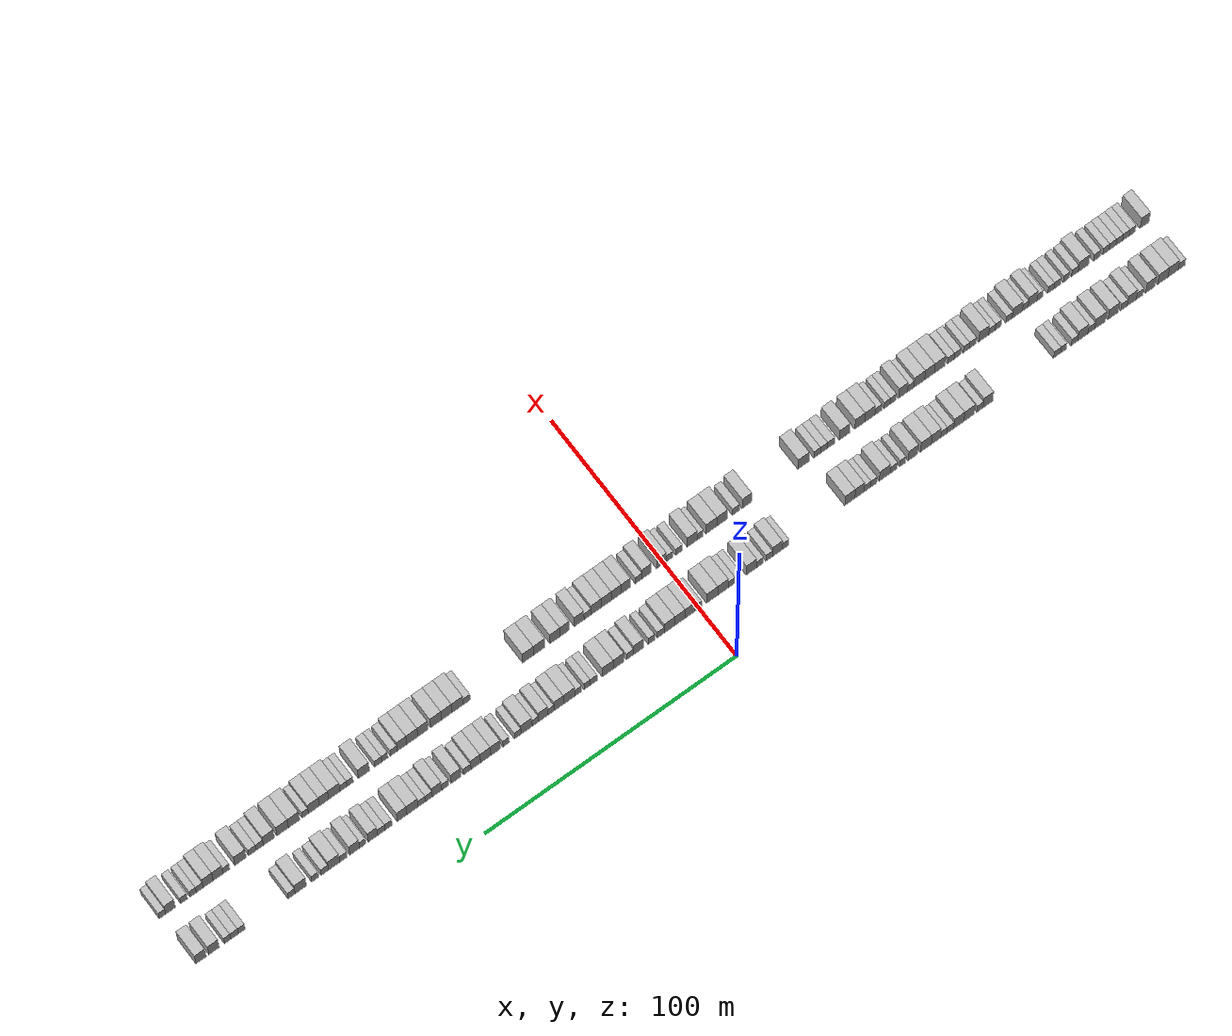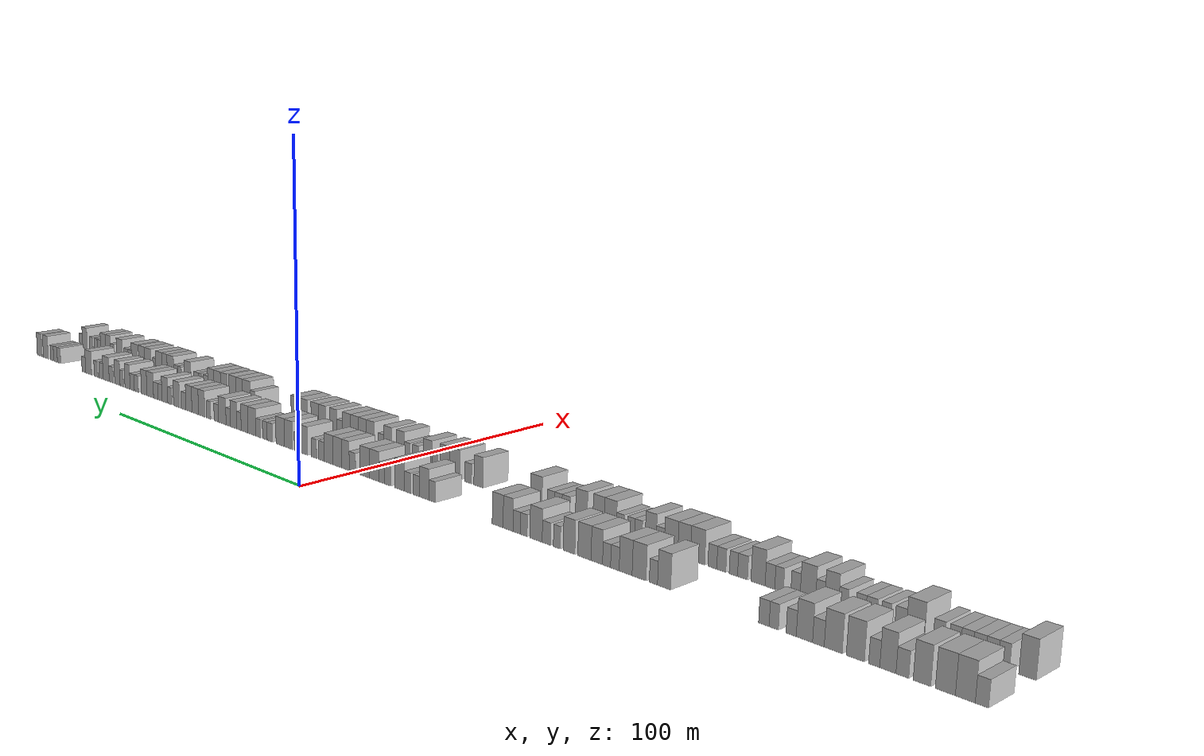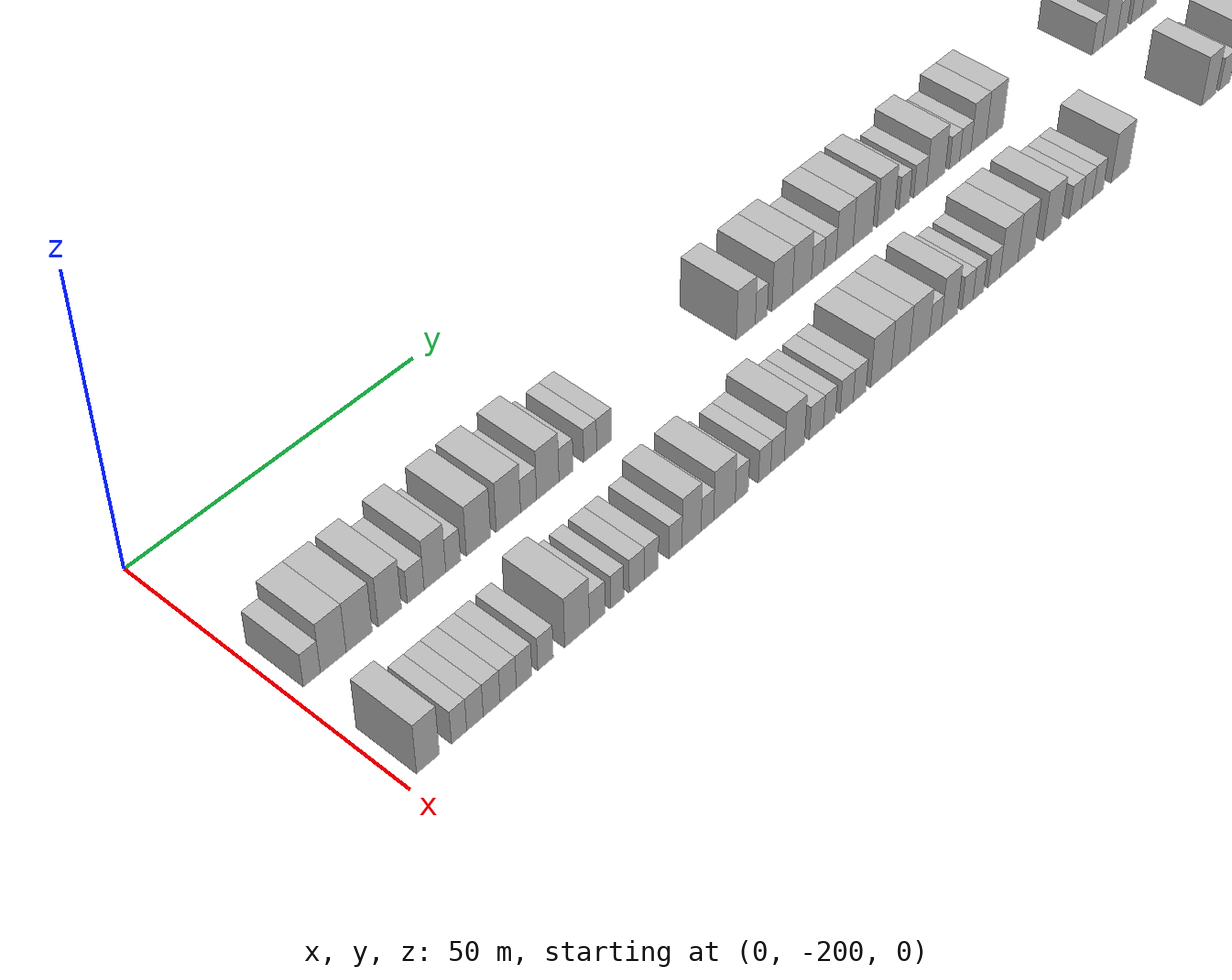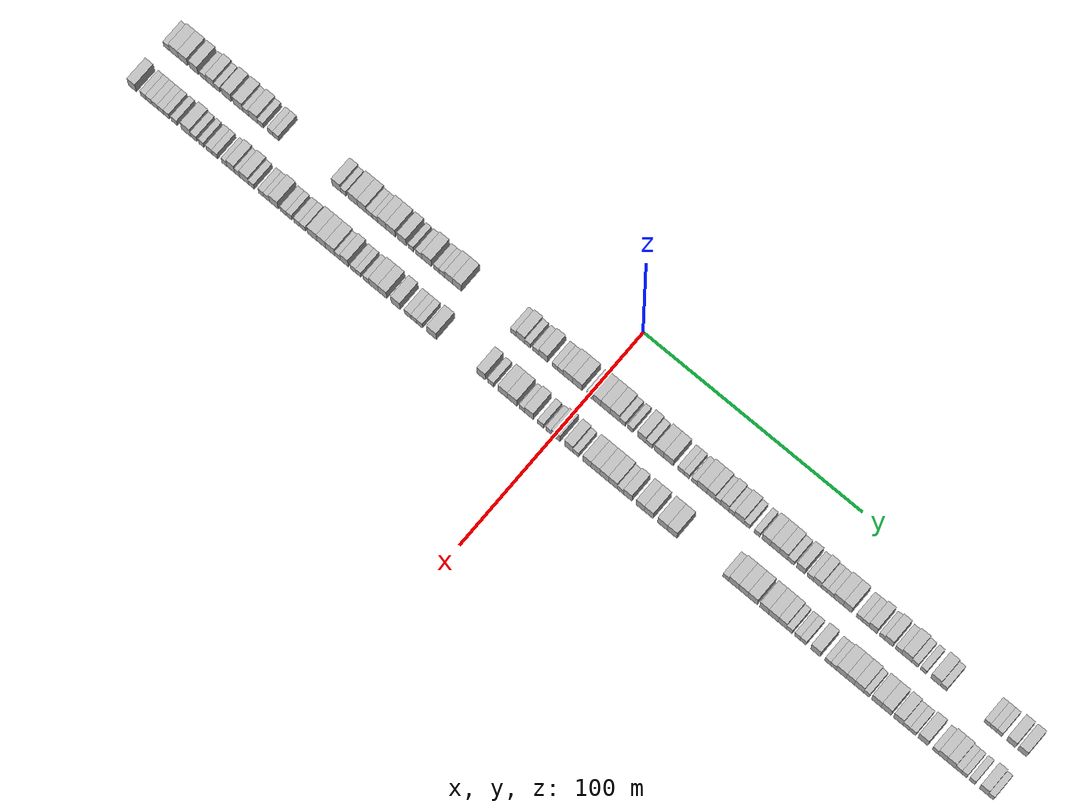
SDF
<sdf version="1.6">
 <world name="default">
  <scene>
   <sky><clouds><speed>12</speed></clouds></sky>
   <ambient>0.4 0.4 0.4 1</ambient>
   <background>0.7 0.7 0.7 1</background>
   <shadows>1</shadows>
  </scene>
  <gravity>0 0 -9.8066</gravity>
  <magnetic_field>6e-06 2.3e-05 -4.2e-05</magnetic_field>
  <physics default="0" name="default_physics" type="ode">
   <ode>
    <solver>
     <type>quick</type>
     <iters>10</iters>
     <sor>1.0</sor>
     <use_dynamic_moi_rescaling>0</use_dynamic_moi_rescaling>
    </solver>
    <constraints>
     <cfm>0</cfm>
     <erp>0.2</erp>
     <contact_max_correcting_vel>100</contact_max_correcting_vel>
     <contact_surface_layer>0.001</contact_surface_layer>
    </constraints>
   </ode>
   <max_step_size>0.004</max_step_size>
   <real_time_factor>1</real_time_factor>
   <real_time_update_rate>250</real_time_update_rate>
  </physics>
  <light name="sun" type="directional">
   <pose>0 0 10 0 0 0</pose>
   <diffuse>0.8 0.8 0.8 1</diffuse>
   <specular>0.2 0.2 0.2 1</specular>
   <attenuation>
    <range>1000</range>
    <constant>0.9</constant>
    <linear>0.01</linear>
    <quadratic>0.001</quadratic>
   </attenuation>
   <direction>-0.5 0.1 -0.9</direction>
  </light>
  <model name="building_1">
   <static>1</static>
   <pose>25.0000 -196.6038 0 0.000000 0.000000 0.000000</pose>
   <link name="link">
    <pose>0 0 3.00 0 0 0</pose>
    <collision name="collision"><geometry><box><size>10.0000 2.7924 6.0000</size></box></geometry></collision>
    <visual name="visual">
     <cast_shadows>0</cast_shadows>
     <geometry><box><size>10.0000 2.7924 6.0000</size></box></geometry>
     <material>
      <script>
       <uri>model://HANNAS_wall/materials/scripts</uri>
       <uri>model://HANNAS_wall/materials/textures</uri>
       <name>vrc/HANNAS_wall</name>
      </script>
     </material>
    </visual>
   </link>
  </model>
  <model name="building_2">
   <static>1</static>
   <pose>25.0000 -193.0920 0 0.000000 0.000000 0.000000</pose>
   <link name="link">
    <pose>0 0 4.50 0 0 0</pose>
    <collision name="collision"><geometry><box><size>10.0000 4.2312 9.0000</size></box></geometry></collision>
    <visual name="visual">
     <cast_shadows>0</cast_shadows>
     <geometry><box><size>10.0000 4.2312 9.0000</size></box></geometry>
     <material>
      <script>
       <uri>model://HANNAS_wall/materials/scripts</uri>
       <uri>model://HANNAS_wall/materials/textures</uri>
       <name>vrc/HANNAS_wall</name>
      </script>
     </material>
    </visual>
   </link>
  </model>
  <model name="building_3">
   <static>1</static>
   <pose>25.0000 -188.8017 0 0.000000 0.000000 0.000000</pose>
   <link name="link">
    <pose>0 0 4.50 0 0 0</pose>
    <collision name="collision"><geometry><box><size>10.0000 4.3494 9.0000</size></box></geometry></collision>
    <visual name="visual">
     <cast_shadows>0</cast_shadows>
     <geometry><box><size>10.0000 4.3494 9.0000</size></box></geometry>
     <material>
      <script>
       <uri>model://HANNAS_wall/materials/scripts</uri>
       <uri>model://HANNAS_wall/materials/textures</uri>
       <name>vrc/HANNAS_wall</name>
      </script>
     </material>
    </visual>
   </link>
  </model>
  <model name="building_4">
   <static>1</static>
   <pose>25.0000 -183.6629 0 0.000000 0.000000 0.000000</pose>
   <link name="link">
    <pose>0 0 4.50 0 0 0</pose>
    <collision name="collision"><geometry><box><size>10.0000 3.9281 9.0000</size></box></geometry></collision>
    <visual name="visual">
     <cast_shadows>0</cast_shadows>
     <geometry><box><size>10.0000 3.9281 9.0000</size></box></geometry>
     <material>
      <script>
       <uri>model://HANNAS_wall/materials/scripts</uri>
       <uri>model://HANNAS_wall/materials/textures</uri>
       <name>vrc/HANNAS_wall</name>
      </script>
     </material>
    </visual>
   </link>
  </model>
  <model name="building_5">
   <static>1</static>
   <pose>25.0000 -179.2473 0 0.000000 0.000000 0.000000</pose>
   <link name="link">
    <pose>0 0 3.00 0 0 0</pose>
    <collision name="collision"><geometry><box><size>10.0000 2.9031 6.0000</size></box></geometry></collision>
    <visual name="visual">
     <cast_shadows>0</cast_shadows>
     <geometry><box><size>10.0000 2.9031 6.0000</size></box></geometry>
     <material>
      <script>
       <uri>model://HANNAS_wall/materials/scripts</uri>
       <uri>model://HANNAS_wall/materials/textures</uri>
       <name>vrc/HANNAS_wall</name>
      </script>
     </material>
    </visual>
   </link>
  </model>
  <model name="building_6">
   <static>1</static>
   <pose>25.0000 -175.9165 0 0.000000 0.000000 0.000000</pose>
   <link name="link">
    <pose>0 0 4.50 0 0 0</pose>
    <collision name="collision"><geometry><box><size>10.0000 3.7585 9.0000</size></box></geometry></collision>
    <visual name="visual">
     <cast_shadows>0</cast_shadows>
     <geometry><box><size>10.0000 3.7585 9.0000</size></box></geometry>
     <material>
      <script>
       <uri>model://HANNAS_wall/materials/scripts</uri>
       <uri>model://HANNAS_wall/materials/textures</uri>
       <name>vrc/HANNAS_wall</name>
      </script>
     </material>
    </visual>
   </link>
  </model>
  <model name="building_7">
   <static>1</static>
   <pose>25.0000 -172.7291 0 0.000000 0.000000 0.000000</pose>
   <link name="link">
    <pose>0 0 3.00 0 0 0</pose>
    <collision name="collision"><geometry><box><size>10.0000 2.6163 6.0000</size></box></geometry></collision>
    <visual name="visual">
     <cast_shadows>0</cast_shadows>
     <geometry><box><size>10.0000 2.6163 6.0000</size></box></geometry>
     <material>
      <script>
       <uri>model://HANNAS_wall/materials/scripts</uri>
       <uri>model://HANNAS_wall/materials/textures</uri>
       <name>vrc/HANNAS_wall</name>
      </script>
     </material>
    </visual>
   </link>
  </model>
  <model name="building_8">
   <static>1</static>
   <pose>25.0000 -168.2506 0 0.000000 0.000000 0.000000</pose>
   <link name="link">
    <pose>0 0 4.50 0 0 0</pose>
    <collision name="collision"><geometry><box><size>10.0000 4.3406 9.0000</size></box></geometry></collision>
    <visual name="visual">
     <cast_shadows>0</cast_shadows>
     <geometry><box><size>10.0000 4.3406 9.0000</size></box></geometry>
     <material>
      <script>
       <uri>model://HANNAS_wall/materials/scripts</uri>
       <uri>model://HANNAS_wall/materials/textures</uri>
       <name>vrc/HANNAS_wall</name>
      </script>
     </material>
    </visual>
   </link>
  </model>
  <model name="building_9">
   <static>1</static>
   <pose>25.0000 -162.8750 0 0.000000 0.000000 0.000000</pose>
   <link name="link">
    <pose>0 0 4.50 0 0 0</pose>
    <collision name="collision"><geometry><box><size>10.0000 4.4108 9.0000</size></box></geometry></collision>
    <visual name="visual">
     <cast_shadows>0</cast_shadows>
     <geometry><box><size>10.0000 4.4108 9.0000</size></box></geometry>
     <material>
      <script>
       <uri>model://HANNAS_wall/materials/scripts</uri>
       <uri>model://HANNAS_wall/materials/textures</uri>
       <name>vrc/HANNAS_wall</name>
      </script>
     </material>
    </visual>
   </link>
  </model>
  <model name="building_10">
   <static>1</static>
   <pose>25.0000 -159.2041 0 0.000000 0.000000 0.000000</pose>
   <link name="link">
    <pose>0 0 3.00 0 0 0</pose>
    <collision name="collision"><geometry><box><size>10.0000 2.9310 6.0000</size></box></geometry></collision>
    <visual name="visual">
     <cast_shadows>0</cast_shadows>
     <geometry><box><size>10.0000 2.9310 6.0000</size></box></geometry>
     <material>
      <script>
       <uri>model://HANNAS_wall/materials/scripts</uri>
       <uri>model://HANNAS_wall/materials/textures</uri>
       <name>vrc/HANNAS_wall</name>
      </script>
     </material>
    </visual>
   </link>
  </model>
  <model name="building_11">
   <static>1</static>
   <pose>25.0000 -155.6651 0 0.000000 0.000000 0.000000</pose>
   <link name="link">
    <pose>0 0 4.50 0 0 0</pose>
    <collision name="collision"><geometry><box><size>10.0000 4.1469 9.0000</size></box></geometry></collision>
    <visual name="visual">
     <cast_shadows>0</cast_shadows>
     <geometry><box><size>10.0000 4.1469 9.0000</size></box></geometry>
     <material>
      <script>
       <uri>model://HANNAS_wall/materials/scripts</uri>
       <uri>model://HANNAS_wall/materials/textures</uri>
       <name>vrc/HANNAS_wall</name>
      </script>
     </material>
    </visual>
   </link>
  </model>
  <model name="building_12">
   <static>1</static>
   <pose>25.0000 -152.2709 0 0.000000 0.000000 0.000000</pose>
   <link name="link">
    <pose>0 0 3.00 0 0 0</pose>
    <collision name="collision"><geometry><box><size>10.0000 2.6415 6.0000</size></box></geometry></collision>
    <visual name="visual">
     <cast_shadows>0</cast_shadows>
     <geometry><box><size>10.0000 2.6415 6.0000</size></box></geometry>
     <material>
      <script>
       <uri>model://HANNAS_wall/materials/scripts</uri>
       <uri>model://HANNAS_wall/materials/textures</uri>
       <name>vrc/HANNAS_wall</name>
      </script>
     </material>
    </visual>
   </link>
  </model>
  <model name="building_13">
   <static>1</static>
   <pose>25.0000 -147.7270 0 0.000000 0.000000 0.000000</pose>
   <link name="link">
    <pose>0 0 3.00 0 0 0</pose>
    <collision name="collision"><geometry><box><size>10.0000 2.4463 6.0000</size></box></geometry></collision>
    <visual name="visual">
     <cast_shadows>0</cast_shadows>
     <geometry><box><size>10.0000 2.4463 6.0000</size></box></geometry>
     <material>
      <script>
       <uri>model://HANNAS_wall/materials/scripts</uri>
       <uri>model://HANNAS_wall/materials/textures</uri>
       <name>vrc/HANNAS_wall</name>
      </script>
     </material>
    </visual>
   </link>
  </model>
  <model name="building_14">
   <static>1</static>
   <pose>25.0000 -145.0984 0 0.000000 0.000000 0.000000</pose>
   <link name="link">
    <pose>0 0 3.00 0 0 0</pose>
    <collision name="collision"><geometry><box><size>10.0000 2.8109 6.0000</size></box></geometry></collision>
    <visual name="visual">
     <cast_shadows>0</cast_shadows>
     <geometry><box><size>10.0000 2.8109 6.0000</size></box></geometry>
     <material>
      <script>
       <uri>model://HANNAS_wall/materials/scripts</uri>
       <uri>model://HANNAS_wall/materials/textures</uri>
       <name>vrc/HANNAS_wall</name>
      </script>
     </material>
    </visual>
   </link>
  </model>
  <model name="building_15">
   <static>1</static>
   <pose>25.0000 -116.7567 0 0.000000 0.000000 0.000000</pose>
   <link name="link">
    <pose>0 0 4.50 0 0 0</pose>
    <collision name="collision"><geometry><box><size>10.0000 3.9575 9.0000</size></box></geometry></collision>
    <visual name="visual">
     <cast_shadows>0</cast_shadows>
     <geometry><box><size>10.0000 3.9575 9.0000</size></box></geometry>
     <material>
      <script>
       <uri>model://HANNAS_wall/materials/scripts</uri>
       <uri>model://HANNAS_wall/materials/textures</uri>
       <name>vrc/HANNAS_wall</name>
      </script>
     </material>
    </visual>
   </link>
  </model>
  <model name="building_16">
   <static>1</static>
   <pose>25.0000 -113.5203 0 0.000000 0.000000 0.000000</pose>
   <link name="link">
    <pose>0 0 3.00 0 0 0</pose>
    <collision name="collision"><geometry><box><size>10.0000 2.5154 6.0000</size></box></geometry></collision>
    <visual name="visual">
     <cast_shadows>0</cast_shadows>
     <geometry><box><size>10.0000 2.5154 6.0000</size></box></geometry>
     <material>
      <script>
       <uri>model://HANNAS_wall/materials/scripts</uri>
       <uri>model://HANNAS_wall/materials/textures</uri>
       <name>vrc/HANNAS_wall</name>
      </script>
     </material>
    </visual>
   </link>
  </model>
  <model name="building_17">
   <static>1</static>
   <pose>25.0000 -109.0836 0 0.000000 0.000000 0.000000</pose>
   <link name="link">
    <pose>0 0 4.50 0 0 0</pose>
    <collision name="collision"><geometry><box><size>10.0000 4.3579 9.0000</size></box></geometry></collision>
    <visual name="visual">
     <cast_shadows>0</cast_shadows>
     <geometry><box><size>10.0000 4.3579 9.0000</size></box></geometry>
     <material>
      <script>
       <uri>model://HANNAS_wall/materials/scripts</uri>
       <uri>model://HANNAS_wall/materials/textures</uri>
       <name>vrc/HANNAS_wall</name>
      </script>
     </material>
    </visual>
   </link>
  </model>
  <model name="building_18">
   <static>1</static>
   <pose>25.0000 -104.8493 0 0.000000 0.000000 0.000000</pose>
   <link name="link">
    <pose>0 0 4.50 0 0 0</pose>
    <collision name="collision"><geometry><box><size>10.0000 4.1108 9.0000</size></box></geometry></collision>
    <visual name="visual">
     <cast_shadows>0</cast_shadows>
     <geometry><box><size>10.0000 4.1108 9.0000</size></box></geometry>
     <material>
      <script>
       <uri>model://HANNAS_wall/materials/scripts</uri>
       <uri>model://HANNAS_wall/materials/textures</uri>
       <name>vrc/HANNAS_wall</name>
      </script>
     </material>
    </visual>
   </link>
  </model>
  <model name="building_19">
   <static>1</static>
   <pose>25.0000 -101.4165 0 0.000000 0.000000 0.000000</pose>
   <link name="link">
    <pose>0 0 3.00 0 0 0</pose>
    <collision name="collision"><geometry><box><size>10.0000 2.7549 6.0000</size></box></geometry></collision>
    <visual name="visual">
     <cast_shadows>0</cast_shadows>
     <geometry><box><size>10.0000 2.7549 6.0000</size></box></geometry>
     <material>
      <script>
       <uri>model://HANNAS_wall/materials/scripts</uri>
       <uri>model://HANNAS_wall/materials/textures</uri>
       <name>vrc/HANNAS_wall</name>
      </script>
     </material>
    </visual>
   </link>
  </model>
  <model name="building_20">
   <static>1</static>
   <pose>25.0000 -98.7303 0 0.000000 0.000000 0.000000</pose>
   <link name="link">
    <pose>0 0 3.00 0 0 0</pose>
    <collision name="collision"><geometry><box><size>10.0000 2.6175 6.0000</size></box></geometry></collision>
    <visual name="visual">
     <cast_shadows>0</cast_shadows>
     <geometry><box><size>10.0000 2.6175 6.0000</size></box></geometry>
     <material>
      <script>
       <uri>model://HANNAS_wall/materials/scripts</uri>
       <uri>model://HANNAS_wall/materials/textures</uri>
       <name>vrc/HANNAS_wall</name>
      </script>
     </material>
    </visual>
   </link>
  </model>
  <model name="building_21">
   <static>1</static>
   <pose>25.0000 -95.5214 0 0.000000 0.000000 0.000000</pose>
   <link name="link">
    <pose>0 0 4.50 0 0 0</pose>
    <collision name="collision"><geometry><box><size>10.0000 3.8002 9.0000</size></box></geometry></collision>
    <visual name="visual">
     <cast_shadows>0</cast_shadows>
     <geometry><box><size>10.0000 3.8002 9.0000</size></box></geometry>
     <material>
      <script>
       <uri>model://HANNAS_wall/materials/scripts</uri>
       <uri>model://HANNAS_wall/materials/textures</uri>
       <name>vrc/HANNAS_wall</name>
      </script>
     </material>
    </visual>
   </link>
  </model>
  <model name="building_22">
   <static>1</static>
   <pose>25.0000 -91.4064 0 0.000000 0.000000 0.000000</pose>
   <link name="link">
    <pose>0 0 4.50 0 0 0</pose>
    <collision name="collision"><geometry><box><size>10.0000 4.4298 9.0000</size></box></geometry></collision>
    <visual name="visual">
     <cast_shadows>0</cast_shadows>
     <geometry><box><size>10.0000 4.4298 9.0000</size></box></geometry>
     <material>
      <script>
       <uri>model://HANNAS_wall/materials/scripts</uri>
       <uri>model://HANNAS_wall/materials/textures</uri>
       <name>vrc/HANNAS_wall</name>
      </script>
     </material>
    </visual>
   </link>
  </model>
  <model name="building_23">
   <static>1</static>
   <pose>25.0000 -86.1940 0 0.000000 0.000000 0.000000</pose>
   <link name="link">
    <pose>0 0 4.50 0 0 0</pose>
    <collision name="collision"><geometry><box><size>10.0000 3.9950 9.0000</size></box></geometry></collision>
    <visual name="visual">
     <cast_shadows>0</cast_shadows>
     <geometry><box><size>10.0000 3.9950 9.0000</size></box></geometry>
     <material>
      <script>
       <uri>model://HANNAS_wall/materials/scripts</uri>
       <uri>model://HANNAS_wall/materials/textures</uri>
       <name>vrc/HANNAS_wall</name>
      </script>
     </material>
    </visual>
   </link>
  </model>
  <model name="building_24">
   <static>1</static>
   <pose>25.0000 -81.9947 0 0.000000 0.000000 0.000000</pose>
   <link name="link">
    <pose>0 0 3.00 0 0 0</pose>
    <collision name="collision"><geometry><box><size>10.0000 2.4037 6.0000</size></box></geometry></collision>
    <visual name="visual">
     <cast_shadows>0</cast_shadows>
     <geometry><box><size>10.0000 2.4037 6.0000</size></box></geometry>
     <material>
      <script>
       <uri>model://HANNAS_wall/materials/scripts</uri>
       <uri>model://HANNAS_wall/materials/textures</uri>
       <name>vrc/HANNAS_wall</name>
      </script>
     </material>
    </visual>
   </link>
  </model>
  <model name="building_25">
   <static>1</static>
   <pose>25.0000 -78.3166 0 0.000000 0.000000 0.000000</pose>
   <link name="link">
    <pose>0 0 3.00 0 0 0</pose>
    <collision name="collision"><geometry><box><size>10.0000 2.9525 6.0000</size></box></geometry></collision>
    <visual name="visual">
     <cast_shadows>0</cast_shadows>
     <geometry><box><size>10.0000 2.9525 6.0000</size></box></geometry>
     <material>
      <script>
       <uri>model://HANNAS_wall/materials/scripts</uri>
       <uri>model://HANNAS_wall/materials/textures</uri>
       <name>vrc/HANNAS_wall</name>
      </script>
     </material>
    </visual>
   </link>
  </model>
  <model name="building_26">
   <static>1</static>
   <pose>25.0000 -74.6427 0 0.000000 0.000000 0.000000</pose>
   <link name="link">
    <pose>0 0 4.50 0 0 0</pose>
    <collision name="collision"><geometry><box><size>10.0000 4.3952 9.0000</size></box></geometry></collision>
    <visual name="visual">
     <cast_shadows>0</cast_shadows>
     <geometry><box><size>10.0000 4.3952 9.0000</size></box></geometry>
     <material>
      <script>
       <uri>model://HANNAS_wall/materials/scripts</uri>
       <uri>model://HANNAS_wall/materials/textures</uri>
       <name>vrc/HANNAS_wall</name>
      </script>
     </material>
    </visual>
   </link>
  </model>
  <model name="building_27">
   <static>1</static>
   <pose>25.0000 -70.2161 0 0.000000 0.000000 0.000000</pose>
   <link name="link">
    <pose>0 0 3.00 0 0 0</pose>
    <collision name="collision"><geometry><box><size>10.0000 2.4581 6.0000</size></box></geometry></collision>
    <visual name="visual">
     <cast_shadows>0</cast_shadows>
     <geometry><box><size>10.0000 2.4581 6.0000</size></box></geometry>
     <material>
      <script>
       <uri>model://HANNAS_wall/materials/scripts</uri>
       <uri>model://HANNAS_wall/materials/textures</uri>
       <name>vrc/HANNAS_wall</name>
      </script>
     </material>
    </visual>
   </link>
  </model>
  <model name="building_28">
   <static>1</static>
   <pose>25.0000 -67.6482 0 0.000000 0.000000 0.000000</pose>
   <link name="link">
    <pose>0 0 3.00 0 0 0</pose>
    <collision name="collision"><geometry><box><size>10.0000 2.6778 6.0000</size></box></geometry></collision>
    <visual name="visual">
     <cast_shadows>0</cast_shadows>
     <geometry><box><size>10.0000 2.6778 6.0000</size></box></geometry>
     <material>
      <script>
       <uri>model://HANNAS_wall/materials/scripts</uri>
       <uri>model://HANNAS_wall/materials/textures</uri>
       <name>vrc/HANNAS_wall</name>
      </script>
     </material>
    </visual>
   </link>
  </model>
  <model name="building_29">
   <static>1</static>
   <pose>25.0000 -64.4440 0 0.000000 0.000000 0.000000</pose>
   <link name="link">
    <pose>0 0 4.50 0 0 0</pose>
    <collision name="collision"><geometry><box><size>10.0000 3.7306 9.0000</size></box></geometry></collision>
    <visual name="visual">
     <cast_shadows>0</cast_shadows>
     <geometry><box><size>10.0000 3.7306 9.0000</size></box></geometry>
     <material>
      <script>
       <uri>model://HANNAS_wall/materials/scripts</uri>
       <uri>model://HANNAS_wall/materials/textures</uri>
       <name>vrc/HANNAS_wall</name>
      </script>
     </material>
    </visual>
   </link>
  </model>
  <model name="building_30">
   <static>1</static>
   <pose>25.0000 -60.5263 0 0.000000 0.000000 0.000000</pose>
   <link name="link">
    <pose>0 0 4.50 0 0 0</pose>
    <collision name="collision"><geometry><box><size>10.0000 4.1048 9.0000</size></box></geometry></collision>
    <visual name="visual">
     <cast_shadows>0</cast_shadows>
     <geometry><box><size>10.0000 4.1048 9.0000</size></box></geometry>
     <material>
      <script>
       <uri>model://HANNAS_wall/materials/scripts</uri>
       <uri>model://HANNAS_wall/materials/textures</uri>
       <name>vrc/HANNAS_wall</name>
      </script>
     </material>
    </visual>
   </link>
  </model>
  <model name="building_31">
   <static>1</static>
   <pose>25.0000 -34.5315 0 0.000000 0.000000 0.000000</pose>
   <link name="link">
    <pose>0 0 3.00 0 0 0</pose>
    <collision name="collision"><geometry><box><size>10.0000 2.6283 6.0000</size></box></geometry></collision>
    <visual name="visual">
     <cast_shadows>0</cast_shadows>
     <geometry><box><size>10.0000 2.6283 6.0000</size></box></geometry>
     <material>
      <script>
       <uri>model://HANNAS_wall/materials/scripts</uri>
       <uri>model://HANNAS_wall/materials/textures</uri>
       <name>vrc/HANNAS_wall</name>
      </script>
     </material>
    </visual>
   </link>
  </model>
  <model name="building_32">
   <static>1</static>
   <pose>25.0000 -31.2306 0 0.000000 0.000000 0.000000</pose>
   <link name="link">
    <pose>0 0 4.50 0 0 0</pose>
    <collision name="collision"><geometry><box><size>10.0000 3.9736 9.0000</size></box></geometry></collision>
    <visual name="visual">
     <cast_shadows>0</cast_shadows>
     <geometry><box><size>10.0000 3.9736 9.0000</size></box></geometry>
     <material>
      <script>
       <uri>model://HANNAS_wall/materials/scripts</uri>
       <uri>model://HANNAS_wall/materials/textures</uri>
       <name>vrc/HANNAS_wall</name>
      </script>
     </material>
    </visual>
   </link>
  </model>
  <model name="building_33">
   <static>1</static>
   <pose>25.0000 -27.9346 0 0.000000 0.000000 0.000000</pose>
   <link name="link">
    <pose>0 0 3.00 0 0 0</pose>
    <collision name="collision"><geometry><box><size>10.0000 2.6184 6.0000</size></box></geometry></collision>
    <visual name="visual">
     <cast_shadows>0</cast_shadows>
     <geometry><box><size>10.0000 2.6184 6.0000</size></box></geometry>
     <material>
      <script>
       <uri>model://HANNAS_wall/materials/scripts</uri>
       <uri>model://HANNAS_wall/materials/textures</uri>
       <name>vrc/HANNAS_wall</name>
      </script>
     </material>
    </visual>
   </link>
  </model>
  <model name="building_34">
   <static>1</static>
   <pose>25.0000 -24.2258 0 0.000000 0.000000 0.000000</pose>
   <link name="link">
    <pose>0 0 3.00 0 0 0</pose>
    <collision name="collision"><geometry><box><size>10.0000 2.7991 6.0000</size></box></geometry></collision>
    <visual name="visual">
     <cast_shadows>0</cast_shadows>
     <geometry><box><size>10.0000 2.7991 6.0000</size></box></geometry>
     <material>
      <script>
       <uri>model://HANNAS_wall/materials/scripts</uri>
       <uri>model://HANNAS_wall/materials/textures</uri>
       <name>vrc/HANNAS_wall</name>
      </script>
     </material>
    </visual>
   </link>
  </model>
  <model name="building_35">
   <static>1</static>
   <pose>25.0000 -20.7856 0 0.000000 0.000000 0.000000</pose>
   <link name="link">
    <pose>0 0 4.50 0 0 0</pose>
    <collision name="collision"><geometry><box><size>10.0000 4.0813 9.0000</size></box></geometry></collision>
    <visual name="visual">
     <cast_shadows>0</cast_shadows>
     <geometry><box><size>10.0000 4.0813 9.0000</size></box></geometry>
     <material>
      <script>
       <uri>model://HANNAS_wall/materials/scripts</uri>
       <uri>model://HANNAS_wall/materials/textures</uri>
       <name>vrc/HANNAS_wall</name>
      </script>
     </material>
    </visual>
   </link>
  </model>
  <model name="building_36">
   <static>1</static>
   <pose>25.0000 -15.4775 0 0.000000 0.000000 0.000000</pose>
   <link name="link">
    <pose>0 0 3.00 0 0 0</pose>
    <collision name="collision"><geometry><box><size>10.0000 2.5350 6.0000</size></box></geometry></collision>
    <visual name="visual">
     <cast_shadows>0</cast_shadows>
     <geometry><box><size>10.0000 2.5350 6.0000</size></box></geometry>
     <material>
      <script>
       <uri>model://HANNAS_wall/materials/scripts</uri>
       <uri>model://HANNAS_wall/materials/textures</uri>
       <name>vrc/HANNAS_wall</name>
      </script>
     </material>
    </visual>
   </link>
  </model>
  <model name="building_37">
   <static>1</static>
   <pose>25.0000 -12.8345 0 0.000000 0.000000 0.000000</pose>
   <link name="link">
    <pose>0 0 3.00 0 0 0</pose>
    <collision name="collision"><geometry><box><size>10.0000 2.7509 6.0000</size></box></geometry></collision>
    <visual name="visual">
     <cast_shadows>0</cast_shadows>
     <geometry><box><size>10.0000 2.7509 6.0000</size></box></geometry>
     <material>
      <script>
       <uri>model://HANNAS_wall/materials/scripts</uri>
       <uri>model://HANNAS_wall/materials/textures</uri>
       <name>vrc/HANNAS_wall</name>
      </script>
     </material>
    </visual>
   </link>
  </model>
  <model name="building_38">
   <static>1</static>
   <pose>25.0000 -9.3605 0 0.000000 0.000000 0.000000</pose>
   <link name="link">
    <pose>0 0 4.50 0 0 0</pose>
    <collision name="collision"><geometry><box><size>10.0000 4.1972 9.0000</size></box></geometry></collision>
    <visual name="visual">
     <cast_shadows>0</cast_shadows>
     <geometry><box><size>10.0000 4.1972 9.0000</size></box></geometry>
     <material>
      <script>
       <uri>model://HANNAS_wall/materials/scripts</uri>
       <uri>model://HANNAS_wall/materials/textures</uri>
       <name>vrc/HANNAS_wall</name>
      </script>
     </material>
    </visual>
   </link>
  </model>
  <model name="building_39">
   <static>1</static>
   <pose>25.0000 -5.0282 0 0.000000 0.000000 0.000000</pose>
   <link name="link">
    <pose>0 0 4.50 0 0 0</pose>
    <collision name="collision"><geometry><box><size>10.0000 4.4674 9.0000</size></box></geometry></collision>
    <visual name="visual">
     <cast_shadows>0</cast_shadows>
     <geometry><box><size>10.0000 4.4674 9.0000</size></box></geometry>
     <material>
      <script>
       <uri>model://HANNAS_wall/materials/scripts</uri>
       <uri>model://HANNAS_wall/materials/textures</uri>
       <name>vrc/HANNAS_wall</name>
      </script>
     </material>
    </visual>
   </link>
  </model>
  <model name="building_40">
   <static>1</static>
   <pose>25.0000 0.6936 0 0.000000 0.000000 0.000000</pose>
   <link name="link">
    <pose>0 0 3.00 0 0 0</pose>
    <collision name="collision"><geometry><box><size>10.0000 2.9762 6.0000</size></box></geometry></collision>
    <visual name="visual">
     <cast_shadows>0</cast_shadows>
     <geometry><box><size>10.0000 2.9762 6.0000</size></box></geometry>
     <material>
      <script>
       <uri>model://HANNAS_wall/materials/scripts</uri>
       <uri>model://HANNAS_wall/materials/textures</uri>
       <name>vrc/HANNAS_wall</name>
      </script>
     </material>
    </visual>
   </link>
  </model>
  <model name="building_41">
   <static>1</static>
   <pose>25.0000 3.9827 0 0.000000 0.000000 0.000000</pose>
   <link name="link">
    <pose>0 0 4.50 0 0 0</pose>
    <collision name="collision"><geometry><box><size>10.0000 3.6018 9.0000</size></box></geometry></collision>
    <visual name="visual">
     <cast_shadows>0</cast_shadows>
     <geometry><box><size>10.0000 3.6018 9.0000</size></box></geometry>
     <material>
      <script>
       <uri>model://HANNAS_wall/materials/scripts</uri>
       <uri>model://HANNAS_wall/materials/textures</uri>
       <name>vrc/HANNAS_wall</name>
      </script>
     </material>
    </visual>
   </link>
  </model>
  <model name="building_42">
   <static>1</static>
   <pose>25.0000 7.8379 0 0.000000 0.000000 0.000000</pose>
   <link name="link">
    <pose>0 0 4.50 0 0 0</pose>
    <collision name="collision"><geometry><box><size>10.0000 4.1087 9.0000</size></box></geometry></collision>
    <visual name="visual">
     <cast_shadows>0</cast_shadows>
     <geometry><box><size>10.0000 4.1087 9.0000</size></box></geometry>
     <material>
      <script>
       <uri>model://HANNAS_wall/materials/scripts</uri>
       <uri>model://HANNAS_wall/materials/textures</uri>
       <name>vrc/HANNAS_wall</name>
      </script>
     </material>
    </visual>
   </link>
  </model>
  <model name="building_43">
   <static>1</static>
   <pose>25.0000 12.0484 0 0.000000 0.000000 0.000000</pose>
   <link name="link">
    <pose>0 0 4.50 0 0 0</pose>
    <collision name="collision"><geometry><box><size>10.0000 4.3123 9.0000</size></box></geometry></collision>
    <visual name="visual">
     <cast_shadows>0</cast_shadows>
     <geometry><box><size>10.0000 4.3123 9.0000</size></box></geometry>
     <material>
      <script>
       <uri>model://HANNAS_wall/materials/scripts</uri>
       <uri>model://HANNAS_wall/materials/textures</uri>
       <name>vrc/HANNAS_wall</name>
      </script>
     </material>
    </visual>
   </link>
  </model>
  <model name="building_44">
   <static>1</static>
   <pose>25.0000 15.6020 0 0.000000 0.000000 0.000000</pose>
   <link name="link">
    <pose>0 0 3.00 0 0 0</pose>
    <collision name="collision"><geometry><box><size>10.0000 2.7947 6.0000</size></box></geometry></collision>
    <visual name="visual">
     <cast_shadows>0</cast_shadows>
     <geometry><box><size>10.0000 2.7947 6.0000</size></box></geometry>
     <material>
      <script>
       <uri>model://HANNAS_wall/materials/scripts</uri>
       <uri>model://HANNAS_wall/materials/textures</uri>
       <name>vrc/HANNAS_wall</name>
      </script>
     </material>
    </visual>
   </link>
  </model>
  <model name="building_45">
   <static>1</static>
   <pose>25.0000 19.2593 0 0.000000 0.000000 0.000000</pose>
   <link name="link">
    <pose>0 0 3.00 0 0 0</pose>
    <collision name="collision"><geometry><box><size>10.0000 2.5199 6.0000</size></box></geometry></collision>
    <visual name="visual">
     <cast_shadows>0</cast_shadows>
     <geometry><box><size>10.0000 2.5199 6.0000</size></box></geometry>
     <material>
      <script>
       <uri>model://HANNAS_wall/materials/scripts</uri>
       <uri>model://HANNAS_wall/materials/textures</uri>
       <name>vrc/HANNAS_wall</name>
      </script>
     </material>
    </visual>
   </link>
  </model>
  <model name="building_46">
   <static>1</static>
   <pose>25.0000 24.4487 0 0.000000 0.000000 0.000000</pose>
   <link name="link">
    <pose>0 0 4.50 0 0 0</pose>
    <collision name="collision"><geometry><box><size>10.0000 3.8589 9.0000</size></box></geometry></collision>
    <visual name="visual">
     <cast_shadows>0</cast_shadows>
     <geometry><box><size>10.0000 3.8589 9.0000</size></box></geometry>
     <material>
      <script>
       <uri>model://HANNAS_wall/materials/scripts</uri>
       <uri>model://HANNAS_wall/materials/textures</uri>
       <name>vrc/HANNAS_wall</name>
      </script>
     </material>
    </visual>
   </link>
  </model>
  <model name="building_47">
   <static>1</static>
   <pose>25.0000 27.8278 0 0.000000 0.000000 0.000000</pose>
   <link name="link">
    <pose>0 0 3.00 0 0 0</pose>
    <collision name="collision"><geometry><box><size>10.0000 2.8993 6.0000</size></box></geometry></collision>
    <visual name="visual">
     <cast_shadows>0</cast_shadows>
     <geometry><box><size>10.0000 2.8993 6.0000</size></box></geometry>
     <material>
      <script>
       <uri>model://HANNAS_wall/materials/scripts</uri>
       <uri>model://HANNAS_wall/materials/textures</uri>
       <name>vrc/HANNAS_wall</name>
      </script>
     </material>
    </visual>
   </link>
  </model>
  <model name="building_48">
   <static>1</static>
   <pose>25.0000 32.3691 0 0.000000 0.000000 0.000000</pose>
   <link name="link">
    <pose>0 0 4.50 0 0 0</pose>
    <collision name="collision"><geometry><box><size>10.0000 4.1834 9.0000</size></box></geometry></collision>
    <visual name="visual">
     <cast_shadows>0</cast_shadows>
     <geometry><box><size>10.0000 4.1834 9.0000</size></box></geometry>
     <material>
      <script>
       <uri>model://HANNAS_wall/materials/scripts</uri>
       <uri>model://HANNAS_wall/materials/textures</uri>
       <name>vrc/HANNAS_wall</name>
      </script>
     </material>
    </visual>
   </link>
  </model>
  <model name="building_49">
   <static>1</static>
   <pose>25.0000 36.6838 0 0.000000 0.000000 0.000000</pose>
   <link name="link">
    <pose>0 0 4.50 0 0 0</pose>
    <collision name="collision"><geometry><box><size>10.0000 4.4460 9.0000</size></box></geometry></collision>
    <visual name="visual">
     <cast_shadows>0</cast_shadows>
     <geometry><box><size>10.0000 4.4460 9.0000</size></box></geometry>
     <material>
      <script>
       <uri>model://HANNAS_wall/materials/scripts</uri>
       <uri>model://HANNAS_wall/materials/textures</uri>
       <name>vrc/HANNAS_wall</name>
      </script>
     </material>
    </visual>
   </link>
  </model>
  <model name="building_50">
   <static>1</static>
   <pose>25.0000 42.2739 0 0.000000 0.000000 0.000000</pose>
   <link name="link">
    <pose>0 0 3.00 0 0 0</pose>
    <collision name="collision"><geometry><box><size>10.0000 2.7342 6.0000</size></box></geometry></collision>
    <visual name="visual">
     <cast_shadows>0</cast_shadows>
     <geometry><box><size>10.0000 2.7342 6.0000</size></box></geometry>
     <material>
      <script>
       <uri>model://HANNAS_wall/materials/scripts</uri>
       <uri>model://HANNAS_wall/materials/textures</uri>
       <name>vrc/HANNAS_wall</name>
      </script>
     </material>
    </visual>
   </link>
  </model>
  <model name="building_51">
   <static>1</static>
   <pose>25.0000 44.8899 0 0.000000 0.000000 0.000000</pose>
   <link name="link">
    <pose>0 0 3.00 0 0 0</pose>
    <collision name="collision"><geometry><box><size>10.0000 2.4979 6.0000</size></box></geometry></collision>
    <visual name="visual">
     <cast_shadows>0</cast_shadows>
     <geometry><box><size>10.0000 2.4979 6.0000</size></box></geometry>
     <material>
      <script>
       <uri>model://HANNAS_wall/materials/scripts</uri>
       <uri>model://HANNAS_wall/materials/textures</uri>
       <name>vrc/HANNAS_wall</name>
      </script>
     </material>
    </visual>
   </link>
  </model>
  <model name="building_52">
   <static>1</static>
   <pose>25.0000 48.4372 0 0.000000 0.000000 0.000000</pose>
   <link name="link">
    <pose>0 0 3.00 0 0 0</pose>
    <collision name="collision"><geometry><box><size>10.0000 2.5965 6.0000</size></box></geometry></collision>
    <visual name="visual">
     <cast_shadows>0</cast_shadows>
     <geometry><box><size>10.0000 2.5965 6.0000</size></box></geometry>
     <material>
      <script>
       <uri>model://HANNAS_wall/materials/scripts</uri>
       <uri>model://HANNAS_wall/materials/textures</uri>
       <name>vrc/HANNAS_wall</name>
      </script>
     </material>
    </visual>
   </link>
  </model>
  <model name="building_53">
   <static>1</static>
   <pose>25.0000 51.9839 0 0.000000 0.000000 0.000000</pose>
   <link name="link">
    <pose>0 0 4.50 0 0 0</pose>
    <collision name="collision"><geometry><box><size>10.0000 4.4969 9.0000</size></box></geometry></collision>
    <visual name="visual">
     <cast_shadows>0</cast_shadows>
     <geometry><box><size>10.0000 4.4969 9.0000</size></box></geometry>
     <material>
      <script>
       <uri>model://HANNAS_wall/materials/scripts</uri>
       <uri>model://HANNAS_wall/materials/textures</uri>
       <name>vrc/HANNAS_wall</name>
      </script>
     </material>
    </visual>
   </link>
  </model>
  <model name="building_54">
   <static>1</static>
   <pose>25.0000 56.1350 0 0.000000 0.000000 0.000000</pose>
   <link name="link">
    <pose>0 0 4.50 0 0 0</pose>
    <collision name="collision"><geometry><box><size>10.0000 3.8052 9.0000</size></box></geometry></collision>
    <visual name="visual">
     <cast_shadows>0</cast_shadows>
     <geometry><box><size>10.0000 3.8052 9.0000</size></box></geometry>
     <material>
      <script>
       <uri>model://HANNAS_wall/materials/scripts</uri>
       <uri>model://HANNAS_wall/materials/textures</uri>
       <name>vrc/HANNAS_wall</name>
      </script>
     </material>
    </visual>
   </link>
  </model>
  <model name="building_55">
   <static>1</static>
   <pose>25.0000 59.2513 0 0.000000 0.000000 0.000000</pose>
   <link name="link">
    <pose>0 0 3.00 0 0 0</pose>
    <collision name="collision"><geometry><box><size>10.0000 2.4275 6.0000</size></box></geometry></collision>
    <visual name="visual">
     <cast_shadows>0</cast_shadows>
     <geometry><box><size>10.0000 2.4275 6.0000</size></box></geometry>
     <material>
      <script>
       <uri>model://HANNAS_wall/materials/scripts</uri>
       <uri>model://HANNAS_wall/materials/textures</uri>
       <name>vrc/HANNAS_wall</name>
      </script>
     </material>
    </visual>
   </link>
  </model>
  <model name="building_56">
   <static>1</static>
   <pose>25.0000 62.3258 0 0.000000 0.000000 0.000000</pose>
   <link name="link">
    <pose>0 0 4.50 0 0 0</pose>
    <collision name="collision"><geometry><box><size>10.0000 3.7214 9.0000</size></box></geometry></collision>
    <visual name="visual">
     <cast_shadows>0</cast_shadows>
     <geometry><box><size>10.0000 3.7214 9.0000</size></box></geometry>
     <material>
      <script>
       <uri>model://HANNAS_wall/materials/scripts</uri>
       <uri>model://HANNAS_wall/materials/textures</uri>
       <name>vrc/HANNAS_wall</name>
      </script>
     </material>
    </visual>
   </link>
  </model>
  <model name="building_57">
   <static>1</static>
   <pose>25.0000 65.4446 0 0.000000 0.000000 0.000000</pose>
   <link name="link">
    <pose>0 0 3.00 0 0 0</pose>
    <collision name="collision"><geometry><box><size>10.0000 2.5163 6.0000</size></box></geometry></collision>
    <visual name="visual">
     <cast_shadows>0</cast_shadows>
     <geometry><box><size>10.0000 2.5163 6.0000</size></box></geometry>
     <material>
      <script>
       <uri>model://HANNAS_wall/materials/scripts</uri>
       <uri>model://HANNAS_wall/materials/textures</uri>
       <name>vrc/HANNAS_wall</name>
      </script>
     </material>
    </visual>
   </link>
  </model>
  <model name="building_58">
   <static>1</static>
   <pose>25.0000 68.9086 0 0.000000 0.000000 0.000000</pose>
   <link name="link">
    <pose>0 0 4.50 0 0 0</pose>
    <collision name="collision"><geometry><box><size>10.0000 4.4116 9.0000</size></box></geometry></collision>
    <visual name="visual">
     <cast_shadows>0</cast_shadows>
     <geometry><box><size>10.0000 4.4116 9.0000</size></box></geometry>
     <material>
      <script>
       <uri>model://HANNAS_wall/materials/scripts</uri>
       <uri>model://HANNAS_wall/materials/textures</uri>
       <name>vrc/HANNAS_wall</name>
      </script>
     </material>
    </visual>
   </link>
  </model>
  <model name="building_59">
   <static>1</static>
   <pose>25.0000 72.4070 0 0.000000 0.000000 0.000000</pose>
   <link name="link">
    <pose>0 0 3.00 0 0 0</pose>
    <collision name="collision"><geometry><box><size>10.0000 2.5852 6.0000</size></box></geometry></collision>
    <visual name="visual">
     <cast_shadows>0</cast_shadows>
     <geometry><box><size>10.0000 2.5852 6.0000</size></box></geometry>
     <material>
      <script>
       <uri>model://HANNAS_wall/materials/scripts</uri>
       <uri>model://HANNAS_wall/materials/textures</uri>
       <name>vrc/HANNAS_wall</name>
      </script>
     </material>
    </visual>
   </link>
  </model>
  <model name="building_60">
   <static>1</static>
   <pose>25.0000 76.9773 0 0.000000 0.000000 0.000000</pose>
   <link name="link">
    <pose>0 0 3.00 0 0 0</pose>
    <collision name="collision"><geometry><box><size>10.0000 2.5554 6.0000</size></box></geometry></collision>
    <visual name="visual">
     <cast_shadows>0</cast_shadows>
     <geometry><box><size>10.0000 2.5554 6.0000</size></box></geometry>
     <material>
      <script>
       <uri>model://HANNAS_wall/materials/scripts</uri>
       <uri>model://HANNAS_wall/materials/textures</uri>
       <name>vrc/HANNAS_wall</name>
      </script>
     </material>
    </visual>
   </link>
  </model>
  <model name="building_61">
   <static>1</static>
   <pose>25.0000 81.1700 0 0.000000 0.000000 0.000000</pose>
   <link name="link">
    <pose>0 0 4.50 0 0 0</pose>
    <collision name="collision"><geometry><box><size>10.0000 3.8300 9.0000</size></box></geometry></collision>
    <visual name="visual">
     <cast_shadows>0</cast_shadows>
     <geometry><box><size>10.0000 3.8300 9.0000</size></box></geometry>
     <material>
      <script>
       <uri>model://HANNAS_wall/materials/scripts</uri>
       <uri>model://HANNAS_wall/materials/textures</uri>
       <name>vrc/HANNAS_wall</name>
      </script>
     </material>
    </visual>
   </link>
  </model>
  <model name="building_62">
   <static>1</static>
   <pose>25.0000 85.1062 0 0.000000 0.000000 0.000000</pose>
   <link name="link">
    <pose>0 0 4.50 0 0 0</pose>
    <collision name="collision"><geometry><box><size>10.0000 4.0424 9.0000</size></box></geometry></collision>
    <visual name="visual">
     <cast_shadows>0</cast_shadows>
     <geometry><box><size>10.0000 4.0424 9.0000</size></box></geometry>
     <material>
      <script>
       <uri>model://HANNAS_wall/materials/scripts</uri>
       <uri>model://HANNAS_wall/materials/textures</uri>
       <name>vrc/HANNAS_wall</name>
      </script>
     </material>
    </visual>
   </link>
  </model>
  <model name="building_63">
   <static>1</static>
   <pose>25.0000 88.9948 0 0.000000 0.000000 0.000000</pose>
   <link name="link">
    <pose>0 0 4.50 0 0 0</pose>
    <collision name="collision"><geometry><box><size>10.0000 3.7349 9.0000</size></box></geometry></collision>
    <visual name="visual">
     <cast_shadows>0</cast_shadows>
     <geometry><box><size>10.0000 3.7349 9.0000</size></box></geometry>
     <material>
      <script>
       <uri>model://HANNAS_wall/materials/scripts</uri>
       <uri>model://HANNAS_wall/materials/textures</uri>
       <name>vrc/HANNAS_wall</name>
      </script>
     </material>
    </visual>
   </link>
  </model>
  <model name="building_64">
   <static>1</static>
   <pose>25.0000 92.3562 0 0.000000 0.000000 0.000000</pose>
   <link name="link">
    <pose>0 0 3.00 0 0 0</pose>
    <collision name="collision"><geometry><box><size>10.0000 2.9879 6.0000</size></box></geometry></collision>
    <visual name="visual">
     <cast_shadows>0</cast_shadows>
     <geometry><box><size>10.0000 2.9879 6.0000</size></box></geometry>
     <material>
      <script>
       <uri>model://HANNAS_wall/materials/scripts</uri>
       <uri>model://HANNAS_wall/materials/textures</uri>
       <name>vrc/HANNAS_wall</name>
      </script>
     </material>
    </visual>
   </link>
  </model>
  <model name="building_65">
   <static>1</static>
   <pose>25.0000 96.7611 0 0.000000 0.000000 0.000000</pose>
   <link name="link">
    <pose>0 0 4.50 0 0 0</pose>
    <collision name="collision"><geometry><box><size>10.0000 3.8219 9.0000</size></box></geometry></collision>
    <visual name="visual">
     <cast_shadows>0</cast_shadows>
     <geometry><box><size>10.0000 3.8219 9.0000</size></box></geometry>
     <material>
      <script>
       <uri>model://HANNAS_wall/materials/scripts</uri>
       <uri>model://HANNAS_wall/materials/textures</uri>
       <name>vrc/HANNAS_wall</name>
      </script>
     </material>
    </visual>
   </link>
  </model>
  <model name="building_66">
   <static>1</static>
   <pose>25.0000 101.0352 0 0.000000 0.000000 0.000000</pose>
   <link name="link">
    <pose>0 0 3.00 0 0 0</pose>
    <collision name="collision"><geometry><box><size>10.0000 2.7263 6.0000</size></box></geometry></collision>
    <visual name="visual">
     <cast_shadows>0</cast_shadows>
     <geometry><box><size>10.0000 2.7263 6.0000</size></box></geometry>
     <material>
      <script>
       <uri>model://HANNAS_wall/materials/scripts</uri>
       <uri>model://HANNAS_wall/materials/textures</uri>
       <name>vrc/HANNAS_wall</name>
      </script>
     </material>
    </visual>
   </link>
  </model>
  <model name="building_67">
   <static>1</static>
   <pose>25.0000 104.2591 0 0.000000 0.000000 0.000000</pose>
   <link name="link">
    <pose>0 0 4.50 0 0 0</pose>
    <collision name="collision"><geometry><box><size>10.0000 3.7215 9.0000</size></box></geometry></collision>
    <visual name="visual">
     <cast_shadows>0</cast_shadows>
     <geometry><box><size>10.0000 3.7215 9.0000</size></box></geometry>
     <material>
      <script>
       <uri>model://HANNAS_wall/materials/scripts</uri>
       <uri>model://HANNAS_wall/materials/textures</uri>
       <name>vrc/HANNAS_wall</name>
      </script>
     </material>
    </visual>
   </link>
  </model>
  <model name="building_68">
   <static>1</static>
   <pose>25.0000 107.4287 0 0.000000 0.000000 0.000000</pose>
   <link name="link">
    <pose>0 0 3.00 0 0 0</pose>
    <collision name="collision"><geometry><box><size>10.0000 2.6176 6.0000</size></box></geometry></collision>
    <visual name="visual">
     <cast_shadows>0</cast_shadows>
     <geometry><box><size>10.0000 2.6176 6.0000</size></box></geometry>
     <material>
      <script>
       <uri>model://HANNAS_wall/materials/scripts</uri>
       <uri>model://HANNAS_wall/materials/textures</uri>
       <name>vrc/HANNAS_wall</name>
      </script>
     </material>
    </visual>
   </link>
  </model>
  <model name="building_69">
   <static>1</static>
   <pose>25.0000 110.2218 0 0.000000 0.000000 0.000000</pose>
   <link name="link">
    <pose>0 0 3.00 0 0 0</pose>
    <collision name="collision"><geometry><box><size>10.0000 2.9687 6.0000</size></box></geometry></collision>
    <visual name="visual">
     <cast_shadows>0</cast_shadows>
     <geometry><box><size>10.0000 2.9687 6.0000</size></box></geometry>
     <material>
      <script>
       <uri>model://HANNAS_wall/materials/scripts</uri>
       <uri>model://HANNAS_wall/materials/textures</uri>
       <name>vrc/HANNAS_wall</name>
      </script>
     </material>
    </visual>
   </link>
  </model>
  <model name="building_70">
   <static>1</static>
   <pose>25.0000 113.9028 0 0.000000 0.000000 0.000000</pose>
   <link name="link">
    <pose>0 0 4.50 0 0 0</pose>
    <collision name="collision"><geometry><box><size>10.0000 4.3933 9.0000</size></box></geometry></collision>
    <visual name="visual">
     <cast_shadows>0</cast_shadows>
     <geometry><box><size>10.0000 4.3933 9.0000</size></box></geometry>
     <material>
      <script>
       <uri>model://HANNAS_wall/materials/scripts</uri>
       <uri>model://HANNAS_wall/materials/textures</uri>
       <name>vrc/HANNAS_wall</name>
      </script>
     </material>
    </visual>
   </link>
  </model>
  <model name="building_71">
   <static>1</static>
   <pose>25.0000 117.9787 0 0.000000 0.000000 0.000000</pose>
   <link name="link">
    <pose>0 0 4.50 0 0 0</pose>
    <collision name="collision"><geometry><box><size>10.0000 3.7585 9.0000</size></box></geometry></collision>
    <visual name="visual">
     <cast_shadows>0</cast_shadows>
     <geometry><box><size>10.0000 3.7585 9.0000</size></box></geometry>
     <material>
      <script>
       <uri>model://HANNAS_wall/materials/scripts</uri>
       <uri>model://HANNAS_wall/materials/textures</uri>
       <name>vrc/HANNAS_wall</name>
      </script>
     </material>
    </visual>
   </link>
  </model>
  <model name="building_72">
   <static>1</static>
   <pose>25.0000 123.2542 0 0.000000 0.000000 0.000000</pose>
   <link name="link">
    <pose>0 0 3.00 0 0 0</pose>
    <collision name="collision"><geometry><box><size>10.0000 2.7925 6.0000</size></box></geometry></collision>
    <visual name="visual">
     <cast_shadows>0</cast_shadows>
     <geometry><box><size>10.0000 2.7925 6.0000</size></box></geometry>
     <material>
      <script>
       <uri>model://HANNAS_wall/materials/scripts</uri>
       <uri>model://HANNAS_wall/materials/textures</uri>
       <name>vrc/HANNAS_wall</name>
      </script>
     </material>
    </visual>
   </link>
  </model>
  <model name="building_73">
   <static>1</static>
   <pose>25.0000 126.1238 0 0.000000 0.000000 0.000000</pose>
   <link name="link">
    <pose>0 0 3.00 0 0 0</pose>
    <collision name="collision"><geometry><box><size>10.0000 2.9467 6.0000</size></box></geometry></collision>
    <visual name="visual">
     <cast_shadows>0</cast_shadows>
     <geometry><box><size>10.0000 2.9467 6.0000</size></box></geometry>
     <material>
      <script>
       <uri>model://HANNAS_wall/materials/scripts</uri>
       <uri>model://HANNAS_wall/materials/textures</uri>
       <name>vrc/HANNAS_wall</name>
      </script>
     </material>
    </visual>
   </link>
  </model>
  <model name="building_74">
   <static>1</static>
   <pose>25.0000 129.4040 0 0.000000 0.000000 0.000000</pose>
   <link name="link">
    <pose>0 0 4.50 0 0 0</pose>
    <collision name="collision"><geometry><box><size>10.0000 3.6136 9.0000</size></box></geometry></collision>
    <visual name="visual">
     <cast_shadows>0</cast_shadows>
     <geometry><box><size>10.0000 3.6136 9.0000</size></box></geometry>
     <material>
      <script>
       <uri>model://HANNAS_wall/materials/scripts</uri>
       <uri>model://HANNAS_wall/materials/textures</uri>
       <name>vrc/HANNAS_wall</name>
      </script>
     </material>
    </visual>
   </link>
  </model>
  <model name="building_75">
   <static>1</static>
   <pose>25.0000 133.4173 0 0.000000 0.000000 0.000000</pose>
   <link name="link">
    <pose>0 0 3.00 0 0 0</pose>
    <collision name="collision"><geometry><box><size>10.0000 2.4130 6.0000</size></box></geometry></collision>
    <visual name="visual">
     <cast_shadows>0</cast_shadows>
     <geometry><box><size>10.0000 2.4130 6.0000</size></box></geometry>
     <material>
      <script>
       <uri>model://HANNAS_wall/materials/scripts</uri>
       <uri>model://HANNAS_wall/materials/textures</uri>
       <name>vrc/HANNAS_wall</name>
      </script>
     </material>
    </visual>
   </link>
  </model>
  <model name="building_76">
   <static>1</static>
   <pose>25.0000 136.5219 0 0.000000 0.000000 0.000000</pose>
   <link name="link">
    <pose>0 0 4.50 0 0 0</pose>
    <collision name="collision"><geometry><box><size>10.0000 3.7963 9.0000</size></box></geometry></collision>
    <visual name="visual">
     <cast_shadows>0</cast_shadows>
     <geometry><box><size>10.0000 3.7963 9.0000</size></box></geometry>
     <material>
      <script>
       <uri>model://HANNAS_wall/materials/scripts</uri>
       <uri>model://HANNAS_wall/materials/textures</uri>
       <name>vrc/HANNAS_wall</name>
      </script>
     </material>
    </visual>
   </link>
  </model>
  <model name="building_77">
   <static>1</static>
   <pose>25.0000 140.9003 0 0.000000 0.000000 0.000000</pose>
   <link name="link">
    <pose>0 0 3.00 0 0 0</pose>
    <collision name="collision"><geometry><box><size>10.0000 2.9605 6.0000</size></box></geometry></collision>
    <visual name="visual">
     <cast_shadows>0</cast_shadows>
     <geometry><box><size>10.0000 2.9605 6.0000</size></box></geometry>
     <material>
      <script>
       <uri>model://HANNAS_wall/materials/scripts</uri>
       <uri>model://HANNAS_wall/materials/textures</uri>
       <name>vrc/HANNAS_wall</name>
      </script>
     </material>
    </visual>
   </link>
  </model>
  <model name="building_78">
   <static>1</static>
   <pose>25.0000 144.5743 0 0.000000 0.000000 0.000000</pose>
   <link name="link">
    <pose>0 0 4.50 0 0 0</pose>
    <collision name="collision"><geometry><box><size>10.0000 4.3875 9.0000</size></box></geometry></collision>
    <visual name="visual">
     <cast_shadows>0</cast_shadows>
     <geometry><box><size>10.0000 4.3875 9.0000</size></box></geometry>
     <material>
      <script>
       <uri>model://HANNAS_wall/materials/scripts</uri>
       <uri>model://HANNAS_wall/materials/textures</uri>
       <name>vrc/HANNAS_wall</name>
      </script>
     </material>
    </visual>
   </link>
  </model>
  <model name="building_79">
   <static>1</static>
   <pose>25.0000 148.1960 0 0.000000 0.000000 0.000000</pose>
   <link name="link">
    <pose>0 0 3.00 0 0 0</pose>
    <collision name="collision"><geometry><box><size>10.0000 2.8558 6.0000</size></box></geometry></collision>
    <visual name="visual">
     <cast_shadows>0</cast_shadows>
     <geometry><box><size>10.0000 2.8558 6.0000</size></box></geometry>
     <material>
      <script>
       <uri>model://HANNAS_wall/materials/scripts</uri>
       <uri>model://HANNAS_wall/materials/textures</uri>
       <name>vrc/HANNAS_wall</name>
      </script>
     </material>
    </visual>
   </link>
  </model>
  <model name="building_80">
   <static>1</static>
   <pose>25.0000 151.9748 0 0.000000 0.000000 0.000000</pose>
   <link name="link">
    <pose>0 0 3.00 0 0 0</pose>
    <collision name="collision"><geometry><box><size>10.0000 2.7018 6.0000</size></box></geometry></collision>
    <visual name="visual">
     <cast_shadows>0</cast_shadows>
     <geometry><box><size>10.0000 2.7018 6.0000</size></box></geometry>
     <material>
      <script>
       <uri>model://HANNAS_wall/materials/scripts</uri>
       <uri>model://HANNAS_wall/materials/textures</uri>
       <name>vrc/HANNAS_wall</name>
      </script>
     </material>
    </visual>
   </link>
  </model>
  <model name="building_81">
   <static>1</static>
   <pose>25.0000 157.5533 0 0.000000 0.000000 0.000000</pose>
   <link name="link">
    <pose>0 0 4.50 0 0 0</pose>
    <collision name="collision"><geometry><box><size>10.0000 4.4551 9.0000</size></box></geometry></collision>
    <visual name="visual">
     <cast_shadows>0</cast_shadows>
     <geometry><box><size>10.0000 4.4551 9.0000</size></box></geometry>
     <material>
      <script>
       <uri>model://HANNAS_wall/materials/scripts</uri>
       <uri>model://HANNAS_wall/materials/textures</uri>
       <name>vrc/HANNAS_wall</name>
      </script>
     </material>
    </visual>
   </link>
  </model>
  <model name="building_82">
   <static>1</static>
   <pose>25.0000 161.1548 0 0.000000 0.000000 0.000000</pose>
   <link name="link">
    <pose>0 0 3.00 0 0 0</pose>
    <collision name="collision"><geometry><box><size>10.0000 2.7479 6.0000</size></box></geometry></collision>
    <visual name="visual">
     <cast_shadows>0</cast_shadows>
     <geometry><box><size>10.0000 2.7479 6.0000</size></box></geometry>
     <material>
      <script>
       <uri>model://HANNAS_wall/materials/scripts</uri>
       <uri>model://HANNAS_wall/materials/textures</uri>
       <name>vrc/HANNAS_wall</name>
      </script>
     </material>
    </visual>
   </link>
  </model>
  <model name="building_83">
   <static>1</static>
   <pose>25.0000 180.5134 0 0.000000 0.000000 0.000000</pose>
   <link name="link">
    <pose>0 0 3.00 0 0 0</pose>
    <collision name="collision"><geometry><box><size>10.0000 2.6564 6.0000</size></box></geometry></collision>
    <visual name="visual">
     <cast_shadows>0</cast_shadows>
     <geometry><box><size>10.0000 2.6564 6.0000</size></box></geometry>
     <material>
      <script>
       <uri>model://HANNAS_wall/materials/scripts</uri>
       <uri>model://HANNAS_wall/materials/textures</uri>
       <name>vrc/HANNAS_wall</name>
      </script>
     </material>
    </visual>
   </link>
  </model>
  <model name="building_84">
   <static>1</static>
   <pose>25.0000 183.2970 0 0.000000 0.000000 0.000000</pose>
   <link name="link">
    <pose>0 0 3.00 0 0 0</pose>
    <collision name="collision"><geometry><box><size>10.0000 2.9107 6.0000</size></box></geometry></collision>
    <visual name="visual">
     <cast_shadows>0</cast_shadows>
     <geometry><box><size>10.0000 2.9107 6.0000</size></box></geometry>
     <material>
      <script>
       <uri>model://HANNAS_wall/materials/scripts</uri>
       <uri>model://HANNAS_wall/materials/textures</uri>
       <name>vrc/HANNAS_wall</name>
      </script>
     </material>
    </visual>
   </link>
  </model>
  <model name="building_85">
   <static>1</static>
   <pose>25.0000 185.9808 0 0.000000 0.000000 0.000000</pose>
   <link name="link">
    <pose>0 0 3.00 0 0 0</pose>
    <collision name="collision"><geometry><box><size>10.0000 2.4571 6.0000</size></box></geometry></collision>
    <visual name="visual">
     <cast_shadows>0</cast_shadows>
     <geometry><box><size>10.0000 2.4571 6.0000</size></box></geometry>
     <material>
      <script>
       <uri>model://HANNAS_wall/materials/scripts</uri>
       <uri>model://HANNAS_wall/materials/textures</uri>
       <name>vrc/HANNAS_wall</name>
      </script>
     </material>
    </visual>
   </link>
  </model>
  <model name="building_86">
   <static>1</static>
   <pose>25.0000 191.2265 0 0.000000 0.000000 0.000000</pose>
   <link name="link">
    <pose>0 0 4.50 0 0 0</pose>
    <collision name="collision"><geometry><box><size>10.0000 4.0342 9.0000</size></box></geometry></collision>
    <visual name="visual">
     <cast_shadows>0</cast_shadows>
     <geometry><box><size>10.0000 4.0342 9.0000</size></box></geometry>
     <material>
      <script>
       <uri>model://HANNAS_wall/materials/scripts</uri>
       <uri>model://HANNAS_wall/materials/textures</uri>
       <name>vrc/HANNAS_wall</name>
      </script>
     </material>
    </visual>
   </link>
  </model>
  <model name="building_87">
   <static>1</static>
   <pose>25.0000 196.2425 0 0.000000 0.000000 0.000000</pose>
   <link name="link">
    <pose>0 0 4.50 0 0 0</pose>
    <collision name="collision"><geometry><box><size>10.0000 3.9979 9.0000</size></box></geometry></collision>
    <visual name="visual">
     <cast_shadows>0</cast_shadows>
     <geometry><box><size>10.0000 3.9979 9.0000</size></box></geometry>
     <material>
      <script>
       <uri>model://HANNAS_wall/materials/scripts</uri>
       <uri>model://HANNAS_wall/materials/textures</uri>
       <name>vrc/HANNAS_wall</name>
      </script>
     </material>
    </visual>
   </link>
  </model>
  <model name="building_88">
   <static>1</static>
   <pose>44.0000 -196.1386 0 0.000000 0.000000 0.000000</pose>
   <link name="link">
    <pose>0 0 4.50 0 0 0</pose>
    <collision name="collision"><geometry><box><size>10.0000 3.7229 9.0000</size></box></geometry></collision>
    <visual name="visual">
     <cast_shadows>0</cast_shadows>
     <geometry><box><size>10.0000 3.7229 9.0000</size></box></geometry>
     <material>
      <script>
       <uri>model://HANNAS_wall/materials/scripts</uri>
       <uri>model://HANNAS_wall/materials/textures</uri>
       <name>vrc/HANNAS_wall</name>
      </script>
     </material>
    </visual>
   </link>
  </model>
  <model name="building_89">
   <static>1</static>
   <pose>44.0000 -191.0056 0 0.000000 0.000000 0.000000</pose>
   <link name="link">
    <pose>0 0 3.00 0 0 0</pose>
    <collision name="collision"><geometry><box><size>10.0000 2.5429 6.0000</size></box></geometry></collision>
    <visual name="visual">
     <cast_shadows>0</cast_shadows>
     <geometry><box><size>10.0000 2.5429 6.0000</size></box></geometry>
     <material>
      <script>
       <uri>model://HANNAS_wall/materials/scripts</uri>
       <uri>model://HANNAS_wall/materials/textures</uri>
       <name>vrc/HANNAS_wall</name>
      </script>
     </material>
    </visual>
   </link>
  </model>
  <model name="building_90">
   <static>1</static>
   <pose>44.0000 -188.3514 0 0.000000 0.000000 0.000000</pose>
   <link name="link">
    <pose>0 0 3.00 0 0 0</pose>
    <collision name="collision"><geometry><box><size>10.0000 2.7656 6.0000</size></box></geometry></collision>
    <visual name="visual">
     <cast_shadows>0</cast_shadows>
     <geometry><box><size>10.0000 2.7656 6.0000</size></box></geometry>
     <material>
      <script>
       <uri>model://HANNAS_wall/materials/scripts</uri>
       <uri>model://HANNAS_wall/materials/textures</uri>
       <name>vrc/HANNAS_wall</name>
      </script>
     </material>
    </visual>
   </link>
  </model>
  <model name="building_91">
   <static>1</static>
   <pose>44.0000 -185.5450 0 0.000000 0.000000 0.000000</pose>
   <link name="link">
    <pose>0 0 3.00 0 0 0</pose>
    <collision name="collision"><geometry><box><size>10.0000 2.8471 6.0000</size></box></geometry></collision>
    <visual name="visual">
     <cast_shadows>0</cast_shadows>
     <geometry><box><size>10.0000 2.8471 6.0000</size></box></geometry>
     <material>
      <script>
       <uri>model://HANNAS_wall/materials/scripts</uri>
       <uri>model://HANNAS_wall/materials/textures</uri>
       <name>vrc/HANNAS_wall</name>
      </script>
     </material>
    </visual>
   </link>
  </model>
  <model name="building_92">
   <static>1</static>
   <pose>44.0000 -182.7298 0 0.000000 0.000000 0.000000</pose>
   <link name="link">
    <pose>0 0 3.00 0 0 0</pose>
    <collision name="collision"><geometry><box><size>10.0000 2.7833 6.0000</size></box></geometry></collision>
    <visual name="visual">
     <cast_shadows>0</cast_shadows>
     <geometry><box><size>10.0000 2.7833 6.0000</size></box></geometry>
     <material>
      <script>
       <uri>model://HANNAS_wall/materials/scripts</uri>
       <uri>model://HANNAS_wall/materials/textures</uri>
       <name>vrc/HANNAS_wall</name>
      </script>
     </material>
    </visual>
   </link>
  </model>
  <model name="building_93">
   <static>1</static>
   <pose>44.0000 -180.0049 0 0.000000 0.000000 0.000000</pose>
   <link name="link">
    <pose>0 0 3.00 0 0 0</pose>
    <collision name="collision"><geometry><box><size>10.0000 2.6665 6.0000</size></box></geometry></collision>
    <visual name="visual">
     <cast_shadows>0</cast_shadows>
     <geometry><box><size>10.0000 2.6665 6.0000</size></box></geometry>
     <material>
      <script>
       <uri>model://HANNAS_wall/materials/scripts</uri>
       <uri>model://HANNAS_wall/materials/textures</uri>
       <name>vrc/HANNAS_wall</name>
      </script>
     </material>
    </visual>
   </link>
  </model>
  <model name="building_94">
   <static>1</static>
   <pose>44.0000 -176.3206 0 0.000000 0.000000 0.000000</pose>
   <link name="link">
    <pose>0 0 3.00 0 0 0</pose>
    <collision name="collision"><geometry><box><size>10.0000 2.7021 6.0000</size></box></geometry></collision>
    <visual name="visual">
     <cast_shadows>0</cast_shadows>
     <geometry><box><size>10.0000 2.7021 6.0000</size></box></geometry>
     <material>
      <script>
       <uri>model://HANNAS_wall/materials/scripts</uri>
       <uri>model://HANNAS_wall/materials/textures</uri>
       <name>vrc/HANNAS_wall</name>
      </script>
     </material>
    </visual>
   </link>
  </model>
  <model name="building_95">
   <static>1</static>
   <pose>44.0000 -170.7812 0 0.000000 0.000000 0.000000</pose>
   <link name="link">
    <pose>0 0 4.50 0 0 0</pose>
    <collision name="collision"><geometry><box><size>10.0000 4.3767 9.0000</size></box></geometry></collision>
    <visual name="visual">
     <cast_shadows>0</cast_shadows>
     <geometry><box><size>10.0000 4.3767 9.0000</size></box></geometry>
     <material>
      <script>
       <uri>model://HANNAS_wall/materials/scripts</uri>
       <uri>model://HANNAS_wall/materials/textures</uri>
       <name>vrc/HANNAS_wall</name>
      </script>
     </material>
    </visual>
   </link>
  </model>
  <model name="building_96">
   <static>1</static>
   <pose>44.0000 -167.1882 0 0.000000 0.000000 0.000000</pose>
   <link name="link">
    <pose>0 0 3.00 0 0 0</pose>
    <collision name="collision"><geometry><box><size>10.0000 2.8095 6.0000</size></box></geometry></collision>
    <visual name="visual">
     <cast_shadows>0</cast_shadows>
     <geometry><box><size>10.0000 2.8095 6.0000</size></box></geometry>
     <material>
      <script>
       <uri>model://HANNAS_wall/materials/scripts</uri>
       <uri>model://HANNAS_wall/materials/textures</uri>
       <name>vrc/HANNAS_wall</name>
      </script>
     </material>
    </visual>
   </link>
  </model>
  <model name="building_97">
   <static>1</static>
   <pose>44.0000 -163.5733 0 0.000000 0.000000 0.000000</pose>
   <link name="link">
    <pose>0 0 3.00 0 0 0</pose>
    <collision name="collision"><geometry><box><size>10.0000 2.4204 6.0000</size></box></geometry></collision>
    <visual name="visual">
     <cast_shadows>0</cast_shadows>
     <geometry><box><size>10.0000 2.4204 6.0000</size></box></geometry>
     <material>
      <script>
       <uri>model://HANNAS_wall/materials/scripts</uri>
       <uri>model://HANNAS_wall/materials/textures</uri>
       <name>vrc/HANNAS_wall</name>
      </script>
     </material>
    </visual>
   </link>
  </model>
  <model name="building_98">
   <static>1</static>
   <pose>44.0000 -159.9438 0 0.000000 0.000000 0.000000</pose>
   <link name="link">
    <pose>0 0 3.00 0 0 0</pose>
    <collision name="collision"><geometry><box><size>10.0000 2.8386 6.0000</size></box></geometry></collision>
    <visual name="visual">
     <cast_shadows>0</cast_shadows>
     <geometry><box><size>10.0000 2.8386 6.0000</size></box></geometry>
     <material>
      <script>
       <uri>model://HANNAS_wall/materials/scripts</uri>
       <uri>model://HANNAS_wall/materials/textures</uri>
       <name>vrc/HANNAS_wall</name>
      </script>
     </material>
    </visual>
   </link>
  </model>
  <model name="building_99">
   <static>1</static>
   <pose>44.0000 -157.2572 0 0.000000 0.000000 0.000000</pose>
   <link name="link">
    <pose>0 0 3.00 0 0 0</pose>
    <collision name="collision"><geometry><box><size>10.0000 2.5347 6.0000</size></box></geometry></collision>
    <visual name="visual">
     <cast_shadows>0</cast_shadows>
     <geometry><box><size>10.0000 2.5347 6.0000</size></box></geometry>
     <material>
      <script>
       <uri>model://HANNAS_wall/materials/scripts</uri>
       <uri>model://HANNAS_wall/materials/textures</uri>
       <name>vrc/HANNAS_wall</name>
      </script>
     </material>
    </visual>
   </link>
  </model>
  <model name="building_100">
   <static>1</static>
   <pose>44.0000 -152.7801 0 0.000000 0.000000 0.000000</pose>
   <link name="link">
    <pose>0 0 3.00 0 0 0</pose>
    <collision name="collision"><geometry><box><size>10.0000 2.4194 6.0000</size></box></geometry></collision>
    <visual name="visual">
     <cast_shadows>0</cast_shadows>
     <geometry><box><size>10.0000 2.4194 6.0000</size></box></geometry>
     <material>
      <script>
       <uri>model://HANNAS_wall/materials/scripts</uri>
       <uri>model://HANNAS_wall/materials/textures</uri>
       <name>vrc/HANNAS_wall</name>
      </script>
     </material>
    </visual>
   </link>
  </model>
  <model name="building_101">
   <static>1</static>
   <pose>44.0000 -149.7493 0 0.000000 0.000000 0.000000</pose>
   <link name="link">
    <pose>0 0 4.50 0 0 0</pose>
    <collision name="collision"><geometry><box><size>10.0000 3.6421 9.0000</size></box></geometry></collision>
    <visual name="visual">
     <cast_shadows>0</cast_shadows>
     <geometry><box><size>10.0000 3.6421 9.0000</size></box></geometry>
     <material>
      <script>
       <uri>model://HANNAS_wall/materials/scripts</uri>
       <uri>model://HANNAS_wall/materials/textures</uri>
       <name>vrc/HANNAS_wall</name>
      </script>
     </material>
    </visual>
   </link>
  </model>
  <model name="building_102">
   <static>1</static>
   <pose>44.0000 -146.7272 0 0.000000 0.000000 0.000000</pose>
   <link name="link">
    <pose>0 0 3.00 0 0 0</pose>
    <collision name="collision"><geometry><box><size>10.0000 2.4022 6.0000</size></box></geometry></collision>
    <visual name="visual">
     <cast_shadows>0</cast_shadows>
     <geometry><box><size>10.0000 2.4022 6.0000</size></box></geometry>
     <material>
      <script>
       <uri>model://HANNAS_wall/materials/scripts</uri>
       <uri>model://HANNAS_wall/materials/textures</uri>
       <name>vrc/HANNAS_wall</name>
      </script>
     </material>
    </visual>
   </link>
  </model>
  <model name="building_103">
   <static>1</static>
   <pose>44.0000 -143.4379 0 0.000000 0.000000 0.000000</pose>
   <link name="link">
    <pose>0 0 4.50 0 0 0</pose>
    <collision name="collision"><geometry><box><size>10.0000 4.1764 9.0000</size></box></geometry></collision>
    <visual name="visual">
     <cast_shadows>0</cast_shadows>
     <geometry><box><size>10.0000 4.1764 9.0000</size></box></geometry>
     <material>
      <script>
       <uri>model://HANNAS_wall/materials/scripts</uri>
       <uri>model://HANNAS_wall/materials/textures</uri>
       <name>vrc/HANNAS_wall</name>
      </script>
     </material>
    </visual>
   </link>
  </model>
  <model name="building_104">
   <static>1</static>
   <pose>44.0000 -140.0681 0 0.000000 0.000000 0.000000</pose>
   <link name="link">
    <pose>0 0 3.00 0 0 0</pose>
    <collision name="collision"><geometry><box><size>10.0000 2.5632 6.0000</size></box></geometry></collision>
    <visual name="visual">
     <cast_shadows>0</cast_shadows>
     <geometry><box><size>10.0000 2.5632 6.0000</size></box></geometry>
     <material>
      <script>
       <uri>model://HANNAS_wall/materials/scripts</uri>
       <uri>model://HANNAS_wall/materials/textures</uri>
       <name>vrc/HANNAS_wall</name>
      </script>
     </material>
    </visual>
   </link>
  </model>
  <model name="building_105">
   <static>1</static>
   <pose>44.0000 -135.5689 0 0.000000 0.000000 0.000000</pose>
   <link name="link">
    <pose>0 0 3.00 0 0 0</pose>
    <collision name="collision"><geometry><box><size>10.0000 2.4352 6.0000</size></box></geometry></collision>
    <visual name="visual">
     <cast_shadows>0</cast_shadows>
     <geometry><box><size>10.0000 2.4352 6.0000</size></box></geometry>
     <material>
      <script>
       <uri>model://HANNAS_wall/materials/scripts</uri>
       <uri>model://HANNAS_wall/materials/textures</uri>
       <name>vrc/HANNAS_wall</name>
      </script>
     </material>
    </visual>
   </link>
  </model>
  <model name="building_106">
   <static>1</static>
   <pose>44.0000 -132.9937 0 0.000000 0.000000 0.000000</pose>
   <link name="link">
    <pose>0 0 3.00 0 0 0</pose>
    <collision name="collision"><geometry><box><size>10.0000 2.7152 6.0000</size></box></geometry></collision>
    <visual name="visual">
     <cast_shadows>0</cast_shadows>
     <geometry><box><size>10.0000 2.7152 6.0000</size></box></geometry>
     <material>
      <script>
       <uri>model://HANNAS_wall/materials/scripts</uri>
       <uri>model://HANNAS_wall/materials/textures</uri>
       <name>vrc/HANNAS_wall</name>
      </script>
     </material>
    </visual>
   </link>
  </model>
  <model name="building_107">
   <static>1</static>
   <pose>44.0000 -129.5985 0 0.000000 0.000000 0.000000</pose>
   <link name="link">
    <pose>0 0 4.50 0 0 0</pose>
    <collision name="collision"><geometry><box><size>10.0000 4.0752 9.0000</size></box></geometry></collision>
    <visual name="visual">
     <cast_shadows>0</cast_shadows>
     <geometry><box><size>10.0000 4.0752 9.0000</size></box></geometry>
     <material>
      <script>
       <uri>model://HANNAS_wall/materials/scripts</uri>
       <uri>model://HANNAS_wall/materials/textures</uri>
       <name>vrc/HANNAS_wall</name>
      </script>
     </material>
    </visual>
   </link>
  </model>
  <model name="building_108">
   <static>1</static>
   <pose>44.0000 -125.1083 0 0.000000 0.000000 0.000000</pose>
   <link name="link">
    <pose>0 0 3.00 0 0 0</pose>
    <collision name="collision"><geometry><box><size>10.0000 2.9052 6.0000</size></box></geometry></collision>
    <visual name="visual">
     <cast_shadows>0</cast_shadows>
     <geometry><box><size>10.0000 2.9052 6.0000</size></box></geometry>
     <material>
      <script>
       <uri>model://HANNAS_wall/materials/scripts</uri>
       <uri>model://HANNAS_wall/materials/textures</uri>
       <name>vrc/HANNAS_wall</name>
      </script>
     </material>
    </visual>
   </link>
  </model>
  <model name="building_109">
   <static>1</static>
   <pose>44.0000 -122.4227 0 0.000000 0.000000 0.000000</pose>
   <link name="link">
    <pose>0 0 3.00 0 0 0</pose>
    <collision name="collision"><geometry><box><size>10.0000 2.4660 6.0000</size></box></geometry></collision>
    <visual name="visual">
     <cast_shadows>0</cast_shadows>
     <geometry><box><size>10.0000 2.4660 6.0000</size></box></geometry>
     <material>
      <script>
       <uri>model://HANNAS_wall/materials/scripts</uri>
       <uri>model://HANNAS_wall/materials/textures</uri>
       <name>vrc/HANNAS_wall</name>
      </script>
     </material>
    </visual>
   </link>
  </model>
  <model name="building_110">
   <static>1</static>
   <pose>44.0000 -118.8265 0 0.000000 0.000000 0.000000</pose>
   <link name="link">
    <pose>0 0 3.00 0 0 0</pose>
    <collision name="collision"><geometry><box><size>10.0000 2.7265 6.0000</size></box></geometry></collision>
    <visual name="visual">
     <cast_shadows>0</cast_shadows>
     <geometry><box><size>10.0000 2.7265 6.0000</size></box></geometry>
     <material>
      <script>
       <uri>model://HANNAS_wall/materials/scripts</uri>
       <uri>model://HANNAS_wall/materials/textures</uri>
       <name>vrc/HANNAS_wall</name>
      </script>
     </material>
    </visual>
   </link>
  </model>
  <model name="building_111">
   <static>1</static>
   <pose>44.0000 -116.1233 0 0.000000 0.000000 0.000000</pose>
   <link name="link">
    <pose>0 0 3.00 0 0 0</pose>
    <collision name="collision"><geometry><box><size>10.0000 2.6799 6.0000</size></box></geometry></collision>
    <visual name="visual">
     <cast_shadows>0</cast_shadows>
     <geometry><box><size>10.0000 2.6799 6.0000</size></box></geometry>
     <material>
      <script>
       <uri>model://HANNAS_wall/materials/scripts</uri>
       <uri>model://HANNAS_wall/materials/textures</uri>
       <name>vrc/HANNAS_wall</name>
      </script>
     </material>
    </visual>
   </link>
  </model>
  <model name="building_112">
   <static>1</static>
   <pose>44.0000 -111.5771 0 0.000000 0.000000 0.000000</pose>
   <link name="link">
    <pose>0 0 4.50 0 0 0</pose>
    <collision name="collision"><geometry><box><size>10.0000 4.4124 9.0000</size></box></geometry></collision>
    <visual name="visual">
     <cast_shadows>0</cast_shadows>
     <geometry><box><size>10.0000 4.4124 9.0000</size></box></geometry>
     <material>
      <script>
       <uri>model://HANNAS_wall/materials/scripts</uri>
       <uri>model://HANNAS_wall/materials/textures</uri>
       <name>vrc/HANNAS_wall</name>
      </script>
     </material>
    </visual>
   </link>
  </model>
  <model name="building_113">
   <static>1</static>
   <pose>44.0000 -107.3920 0 0.000000 0.000000 0.000000</pose>
   <link name="link">
    <pose>0 0 4.50 0 0 0</pose>
    <collision name="collision"><geometry><box><size>10.0000 3.9578 9.0000</size></box></geometry></collision>
    <visual name="visual">
     <cast_shadows>0</cast_shadows>
     <geometry><box><size>10.0000 3.9578 9.0000</size></box></geometry>
     <material>
      <script>
       <uri>model://HANNAS_wall/materials/scripts</uri>
       <uri>model://HANNAS_wall/materials/textures</uri>
       <name>vrc/HANNAS_wall</name>
      </script>
     </material>
    </visual>
   </link>
  </model>
  <model name="building_114">
   <static>1</static>
   <pose>44.0000 -103.2288 0 0.000000 0.000000 0.000000</pose>
   <link name="link">
    <pose>0 0 4.50 0 0 0</pose>
    <collision name="collision"><geometry><box><size>10.0000 4.3687 9.0000</size></box></geometry></collision>
    <visual name="visual">
     <cast_shadows>0</cast_shadows>
     <geometry><box><size>10.0000 4.3687 9.0000</size></box></geometry>
     <material>
      <script>
       <uri>model://HANNAS_wall/materials/scripts</uri>
       <uri>model://HANNAS_wall/materials/textures</uri>
       <name>vrc/HANNAS_wall</name>
      </script>
     </material>
    </visual>
   </link>
  </model>
  <model name="building_115">
   <static>1</static>
   <pose>44.0000 -99.7299 0 0.000000 0.000000 0.000000</pose>
   <link name="link">
    <pose>0 0 3.00 0 0 0</pose>
    <collision name="collision"><geometry><box><size>10.0000 2.6290 6.0000</size></box></geometry></collision>
    <visual name="visual">
     <cast_shadows>0</cast_shadows>
     <geometry><box><size>10.0000 2.6290 6.0000</size></box></geometry>
     <material>
      <script>
       <uri>model://HANNAS_wall/materials/scripts</uri>
       <uri>model://HANNAS_wall/materials/textures</uri>
       <name>vrc/HANNAS_wall</name>
      </script>
     </material>
    </visual>
   </link>
  </model>
  <model name="building_116">
   <static>1</static>
   <pose>44.0000 -96.6066 0 0.000000 0.000000 0.000000</pose>
   <link name="link">
    <pose>0 0 4.50 0 0 0</pose>
    <collision name="collision"><geometry><box><size>10.0000 3.6176 9.0000</size></box></geometry></collision>
    <visual name="visual">
     <cast_shadows>0</cast_shadows>
     <geometry><box><size>10.0000 3.6176 9.0000</size></box></geometry>
     <material>
      <script>
       <uri>model://HANNAS_wall/materials/scripts</uri>
       <uri>model://HANNAS_wall/materials/textures</uri>
       <name>vrc/HANNAS_wall</name>
      </script>
     </material>
    </visual>
   </link>
  </model>
  <model name="building_117">
   <static>1</static>
   <pose>44.0000 -92.5390 0 0.000000 0.000000 0.000000</pose>
   <link name="link">
    <pose>0 0 3.00 0 0 0</pose>
    <collision name="collision"><geometry><box><size>10.0000 2.5174 6.0000</size></box></geometry></collision>
    <visual name="visual">
     <cast_shadows>0</cast_shadows>
     <geometry><box><size>10.0000 2.5174 6.0000</size></box></geometry>
     <material>
      <script>
       <uri>model://HANNAS_wall/materials/scripts</uri>
       <uri>model://HANNAS_wall/materials/textures</uri>
       <name>vrc/HANNAS_wall</name>
      </script>
     </material>
    </visual>
   </link>
  </model>
  <model name="building_118">
   <static>1</static>
   <pose>44.0000 -90.0744 0 0.000000 0.000000 0.000000</pose>
   <link name="link">
    <pose>0 0 3.00 0 0 0</pose>
    <collision name="collision"><geometry><box><size>10.0000 2.4119 6.0000</size></box></geometry></collision>
    <visual name="visual">
     <cast_shadows>0</cast_shadows>
     <geometry><box><size>10.0000 2.4119 6.0000</size></box></geometry>
     <material>
      <script>
       <uri>model://HANNAS_wall/materials/scripts</uri>
       <uri>model://HANNAS_wall/materials/textures</uri>
       <name>vrc/HANNAS_wall</name>
      </script>
     </material>
    </visual>
   </link>
  </model>
  <model name="building_119">
   <static>1</static>
   <pose>44.0000 -86.5022 0 0.000000 0.000000 0.000000</pose>
   <link name="link">
    <pose>0 0 3.00 0 0 0</pose>
    <collision name="collision"><geometry><box><size>10.0000 2.7326 6.0000</size></box></geometry></collision>
    <visual name="visual">
     <cast_shadows>0</cast_shadows>
     <geometry><box><size>10.0000 2.7326 6.0000</size></box></geometry>
     <material>
      <script>
       <uri>model://HANNAS_wall/materials/scripts</uri>
       <uri>model://HANNAS_wall/materials/textures</uri>
       <name>vrc/HANNAS_wall</name>
      </script>
     </material>
    </visual>
   </link>
  </model>
  <model name="building_120">
   <static>1</static>
   <pose>44.0000 -83.0468 0 0.000000 0.000000 0.000000</pose>
   <link name="link">
    <pose>0 0 4.50 0 0 0</pose>
    <collision name="collision"><geometry><box><size>10.0000 4.1783 9.0000</size></box></geometry></collision>
    <visual name="visual">
     <cast_shadows>0</cast_shadows>
     <geometry><box><size>10.0000 4.1783 9.0000</size></box></geometry>
     <material>
      <script>
       <uri>model://HANNAS_wall/materials/scripts</uri>
       <uri>model://HANNAS_wall/materials/textures</uri>
       <name>vrc/HANNAS_wall</name>
      </script>
     </material>
    </visual>
   </link>
  </model>
  <model name="building_121">
   <static>1</static>
   <pose>44.0000 -78.9485 0 0.000000 0.000000 0.000000</pose>
   <link name="link">
    <pose>0 0 4.50 0 0 0</pose>
    <collision name="collision"><geometry><box><size>10.0000 4.0183 9.0000</size></box></geometry></collision>
    <visual name="visual">
     <cast_shadows>0</cast_shadows>
     <geometry><box><size>10.0000 4.0183 9.0000</size></box></geometry>
     <material>
      <script>
       <uri>model://HANNAS_wall/materials/scripts</uri>
       <uri>model://HANNAS_wall/materials/textures</uri>
       <name>vrc/HANNAS_wall</name>
      </script>
     </material>
    </visual>
   </link>
  </model>
  <model name="building_122">
   <static>1</static>
   <pose>44.0000 -72.8353 0 0.000000 0.000000 0.000000</pose>
   <link name="link">
    <pose>0 0 4.50 0 0 0</pose>
    <collision name="collision"><geometry><box><size>10.0000 4.2082 9.0000</size></box></geometry></collision>
    <visual name="visual">
     <cast_shadows>0</cast_shadows>
     <geometry><box><size>10.0000 4.2082 9.0000</size></box></geometry>
     <material>
      <script>
       <uri>model://HANNAS_wall/materials/scripts</uri>
       <uri>model://HANNAS_wall/materials/textures</uri>
       <name>vrc/HANNAS_wall</name>
      </script>
     </material>
    </visual>
   </link>
  </model>
  <model name="building_123">
   <static>1</static>
   <pose>44.0000 -67.2592 0 0.000000 0.000000 0.000000</pose>
   <link name="link">
    <pose>0 0 3.00 0 0 0</pose>
    <collision name="collision"><geometry><box><size>10.0000 2.9440 6.0000</size></box></geometry></collision>
    <visual name="visual">
     <cast_shadows>0</cast_shadows>
     <geometry><box><size>10.0000 2.9440 6.0000</size></box></geometry>
     <material>
      <script>
       <uri>model://HANNAS_wall/materials/scripts</uri>
       <uri>model://HANNAS_wall/materials/textures</uri>
       <name>vrc/HANNAS_wall</name>
      </script>
     </material>
    </visual>
   </link>
  </model>
  <model name="building_124">
   <static>1</static>
   <pose>44.0000 -64.3868 0 0.000000 0.000000 0.000000</pose>
   <link name="link">
    <pose>0 0 3.00 0 0 0</pose>
    <collision name="collision"><geometry><box><size>10.0000 2.8008 6.0000</size></box></geometry></collision>
    <visual name="visual">
     <cast_shadows>0</cast_shadows>
     <geometry><box><size>10.0000 2.8008 6.0000</size></box></geometry>
     <material>
      <script>
       <uri>model://HANNAS_wall/materials/scripts</uri>
       <uri>model://HANNAS_wall/materials/textures</uri>
       <name>vrc/HANNAS_wall</name>
      </script>
     </material>
    </visual>
   </link>
  </model>
  <model name="building_125">
   <static>1</static>
   <pose>44.0000 -61.6727 0 0.000000 0.000000 0.000000</pose>
   <link name="link">
    <pose>0 0 3.00 0 0 0</pose>
    <collision name="collision"><geometry><box><size>10.0000 2.6275 6.0000</size></box></geometry></collision>
    <visual name="visual">
     <cast_shadows>0</cast_shadows>
     <geometry><box><size>10.0000 2.6275 6.0000</size></box></geometry>
     <material>
      <script>
       <uri>model://HANNAS_wall/materials/scripts</uri>
       <uri>model://HANNAS_wall/materials/textures</uri>
       <name>vrc/HANNAS_wall</name>
      </script>
     </material>
    </visual>
   </link>
  </model>
  <model name="building_126">
   <static>1</static>
   <pose>44.0000 -56.1247 0 0.000000 0.000000 0.000000</pose>
   <link name="link">
    <pose>0 0 4.50 0 0 0</pose>
    <collision name="collision"><geometry><box><size>10.0000 4.4686 9.0000</size></box></geometry></collision>
    <visual name="visual">
     <cast_shadows>0</cast_shadows>
     <geometry><box><size>10.0000 4.4686 9.0000</size></box></geometry>
     <material>
      <script>
       <uri>model://HANNAS_wall/materials/scripts</uri>
       <uri>model://HANNAS_wall/materials/textures</uri>
       <name>vrc/HANNAS_wall</name>
      </script>
     </material>
    </visual>
   </link>
  </model>
  <model name="building_127">
   <static>1</static>
   <pose>44.0000 -33.1978 0 0.000000 0.000000 0.000000</pose>
   <link name="link">
    <pose>0 0 4.50 0 0 0</pose>
    <collision name="collision"><geometry><box><size>10.0000 3.7950 9.0000</size></box></geometry></collision>
    <visual name="visual">
     <cast_shadows>0</cast_shadows>
     <geometry><box><size>10.0000 3.7950 9.0000</size></box></geometry>
     <material>
      <script>
       <uri>model://HANNAS_wall/materials/scripts</uri>
       <uri>model://HANNAS_wall/materials/textures</uri>
       <name>vrc/HANNAS_wall</name>
      </script>
     </material>
    </visual>
   </link>
  </model>
  <model name="building_128">
   <static>1</static>
   <pose>44.0000 -28.8617 0 0.000000 0.000000 0.000000</pose>
   <link name="link">
    <pose>0 0 3.00 0 0 0</pose>
    <collision name="collision"><geometry><box><size>10.0000 2.8772 6.0000</size></box></geometry></collision>
    <visual name="visual">
     <cast_shadows>0</cast_shadows>
     <geometry><box><size>10.0000 2.8772 6.0000</size></box></geometry>
     <material>
      <script>
       <uri>model://HANNAS_wall/materials/scripts</uri>
       <uri>model://HANNAS_wall/materials/textures</uri>
       <name>vrc/HANNAS_wall</name>
      </script>
     </material>
    </visual>
   </link>
  </model>
  <model name="building_129">
   <static>1</static>
   <pose>44.0000 -23.2683 0 0.000000 0.000000 0.000000</pose>
   <link name="link">
    <pose>0 0 4.50 0 0 0</pose>
    <collision name="collision"><geometry><box><size>10.0000 4.3095 9.0000</size></box></geometry></collision>
    <visual name="visual">
     <cast_shadows>0</cast_shadows>
     <geometry><box><size>10.0000 4.3095 9.0000</size></box></geometry>
     <material>
      <script>
       <uri>model://HANNAS_wall/materials/scripts</uri>
       <uri>model://HANNAS_wall/materials/textures</uri>
       <name>vrc/HANNAS_wall</name>
      </script>
     </material>
    </visual>
   </link>
  </model>
  <model name="building_130">
   <static>1</static>
   <pose>44.0000 -18.9022 0 0.000000 0.000000 0.000000</pose>
   <link name="link">
    <pose>0 0 4.50 0 0 0</pose>
    <collision name="collision"><geometry><box><size>10.0000 4.4229 9.0000</size></box></geometry></collision>
    <visual name="visual">
     <cast_shadows>0</cast_shadows>
     <geometry><box><size>10.0000 4.4229 9.0000</size></box></geometry>
     <material>
      <script>
       <uri>model://HANNAS_wall/materials/scripts</uri>
       <uri>model://HANNAS_wall/materials/textures</uri>
       <name>vrc/HANNAS_wall</name>
      </script>
     </material>
    </visual>
   </link>
  </model>
  <model name="building_131">
   <static>1</static>
   <pose>44.0000 -14.4668 0 0.000000 0.000000 0.000000</pose>
   <link name="link">
    <pose>0 0 3.00 0 0 0</pose>
    <collision name="collision"><geometry><box><size>10.0000 2.4480 6.0000</size></box></geometry></collision>
    <visual name="visual">
     <cast_shadows>0</cast_shadows>
     <geometry><box><size>10.0000 2.4480 6.0000</size></box></geometry>
     <material>
      <script>
       <uri>model://HANNAS_wall/materials/scripts</uri>
       <uri>model://HANNAS_wall/materials/textures</uri>
       <name>vrc/HANNAS_wall</name>
      </script>
     </material>
    </visual>
   </link>
  </model>
  <model name="building_132">
   <static>1</static>
   <pose>44.0000 -11.2497 0 0.000000 0.000000 0.000000</pose>
   <link name="link">
    <pose>0 0 4.50 0 0 0</pose>
    <collision name="collision"><geometry><box><size>10.0000 3.9861 9.0000</size></box></geometry></collision>
    <visual name="visual">
     <cast_shadows>0</cast_shadows>
     <geometry><box><size>10.0000 3.9861 9.0000</size></box></geometry>
     <material>
      <script>
       <uri>model://HANNAS_wall/materials/scripts</uri>
       <uri>model://HANNAS_wall/materials/textures</uri>
       <name>vrc/HANNAS_wall</name>
      </script>
     </material>
    </visual>
   </link>
  </model>
  <model name="building_133">
   <static>1</static>
   <pose>44.0000 -5.8729 0 0.000000 0.000000 0.000000</pose>
   <link name="link">
    <pose>0 0 3.00 0 0 0</pose>
    <collision name="collision"><geometry><box><size>10.0000 2.7675 6.0000</size></box></geometry></collision>
    <visual name="visual">
     <cast_shadows>0</cast_shadows>
     <geometry><box><size>10.0000 2.7675 6.0000</size></box></geometry>
     <material>
      <script>
       <uri>model://HANNAS_wall/materials/scripts</uri>
       <uri>model://HANNAS_wall/materials/textures</uri>
       <name>vrc/HANNAS_wall</name>
      </script>
     </material>
    </visual>
   </link>
  </model>
  <model name="building_134">
   <static>1</static>
   <pose>44.0000 -2.1772 0 0.000000 0.000000 0.000000</pose>
   <link name="link">
    <pose>0 0 3.00 0 0 0</pose>
    <collision name="collision"><geometry><box><size>10.0000 2.6240 6.0000</size></box></geometry></collision>
    <visual name="visual">
     <cast_shadows>0</cast_shadows>
     <geometry><box><size>10.0000 2.6240 6.0000</size></box></geometry>
     <material>
      <script>
       <uri>model://HANNAS_wall/materials/scripts</uri>
       <uri>model://HANNAS_wall/materials/textures</uri>
       <name>vrc/HANNAS_wall</name>
      </script>
     </material>
    </visual>
   </link>
  </model>
  <model name="building_135">
   <static>1</static>
   <pose>44.0000 1.1125 0 0.000000 0.000000 0.000000</pose>
   <link name="link">
    <pose>0 0 4.50 0 0 0</pose>
    <collision name="collision"><geometry><box><size>10.0000 3.9554 9.0000</size></box></geometry></collision>
    <visual name="visual">
     <cast_shadows>0</cast_shadows>
     <geometry><box><size>10.0000 3.9554 9.0000</size></box></geometry>
     <material>
      <script>
       <uri>model://HANNAS_wall/materials/scripts</uri>
       <uri>model://HANNAS_wall/materials/textures</uri>
       <name>vrc/HANNAS_wall</name>
      </script>
     </material>
    </visual>
   </link>
  </model>
  <model name="building_136">
   <static>1</static>
   <pose>44.0000 7.0386 0 0.000000 0.000000 0.000000</pose>
   <link name="link">
    <pose>0 0 4.50 0 0 0</pose>
    <collision name="collision"><geometry><box><size>10.0000 3.8967 9.0000</size></box></geometry></collision>
    <visual name="visual">
     <cast_shadows>0</cast_shadows>
     <geometry><box><size>10.0000 3.8967 9.0000</size></box></geometry>
     <material>
      <script>
       <uri>model://HANNAS_wall/materials/scripts</uri>
       <uri>model://HANNAS_wall/materials/textures</uri>
       <name>vrc/HANNAS_wall</name>
      </script>
     </material>
    </visual>
   </link>
  </model>
  <model name="building_137">
   <static>1</static>
   <pose>44.0000 10.2930 0 0.000000 0.000000 0.000000</pose>
   <link name="link">
    <pose>0 0 3.00 0 0 0</pose>
    <collision name="collision"><geometry><box><size>10.0000 2.6122 6.0000</size></box></geometry></collision>
    <visual name="visual">
     <cast_shadows>0</cast_shadows>
     <geometry><box><size>10.0000 2.6122 6.0000</size></box></geometry>
     <material>
      <script>
       <uri>model://HANNAS_wall/materials/scripts</uri>
       <uri>model://HANNAS_wall/materials/textures</uri>
       <name>vrc/HANNAS_wall</name>
      </script>
     </material>
    </visual>
   </link>
  </model>
  <model name="building_138">
   <static>1</static>
   <pose>44.0000 15.4236 0 0.000000 0.000000 0.000000</pose>
   <link name="link">
    <pose>0 0 4.50 0 0 0</pose>
    <collision name="collision"><geometry><box><size>10.0000 3.6492 9.0000</size></box></geometry></collision>
    <visual name="visual">
     <cast_shadows>0</cast_shadows>
     <geometry><box><size>10.0000 3.6492 9.0000</size></box></geometry>
     <material>
      <script>
       <uri>model://HANNAS_wall/materials/scripts</uri>
       <uri>model://HANNAS_wall/materials/textures</uri>
       <name>vrc/HANNAS_wall</name>
      </script>
     </material>
    </visual>
   </link>
  </model>
  <model name="building_139">
   <static>1</static>
   <pose>44.0000 19.2238 0 0.000000 0.000000 0.000000</pose>
   <link name="link">
    <pose>0 0 4.50 0 0 0</pose>
    <collision name="collision"><geometry><box><size>10.0000 3.9513 9.0000</size></box></geometry></collision>
    <visual name="visual">
     <cast_shadows>0</cast_shadows>
     <geometry><box><size>10.0000 3.9513 9.0000</size></box></geometry>
     <material>
      <script>
       <uri>model://HANNAS_wall/materials/scripts</uri>
       <uri>model://HANNAS_wall/materials/textures</uri>
       <name>vrc/HANNAS_wall</name>
      </script>
     </material>
    </visual>
   </link>
  </model>
  <model name="building_140">
   <static>1</static>
   <pose>44.0000 23.1921 0 0.000000 0.000000 0.000000</pose>
   <link name="link">
    <pose>0 0 4.50 0 0 0</pose>
    <collision name="collision"><geometry><box><size>10.0000 3.9852 9.0000</size></box></geometry></collision>
    <visual name="visual">
     <cast_shadows>0</cast_shadows>
     <geometry><box><size>10.0000 3.9852 9.0000</size></box></geometry>
     <material>
      <script>
       <uri>model://HANNAS_wall/materials/scripts</uri>
       <uri>model://HANNAS_wall/materials/textures</uri>
       <name>vrc/HANNAS_wall</name>
      </script>
     </material>
    </visual>
   </link>
  </model>
  <model name="building_141">
   <static>1</static>
   <pose>44.0000 27.2405 0 0.000000 0.000000 0.000000</pose>
   <link name="link">
    <pose>0 0 4.50 0 0 0</pose>
    <collision name="collision"><geometry><box><size>10.0000 4.1117 9.0000</size></box></geometry></collision>
    <visual name="visual">
     <cast_shadows>0</cast_shadows>
     <geometry><box><size>10.0000 4.1117 9.0000</size></box></geometry>
     <material>
      <script>
       <uri>model://HANNAS_wall/materials/scripts</uri>
       <uri>model://HANNAS_wall/materials/textures</uri>
       <name>vrc/HANNAS_wall</name>
      </script>
     </material>
    </visual>
   </link>
  </model>
  <model name="building_142">
   <static>1</static>
   <pose>44.0000 30.7181 0 0.000000 0.000000 0.000000</pose>
   <link name="link">
    <pose>0 0 3.00 0 0 0</pose>
    <collision name="collision"><geometry><box><size>10.0000 2.8433 6.0000</size></box></geometry></collision>
    <visual name="visual">
     <cast_shadows>0</cast_shadows>
     <geometry><box><size>10.0000 2.8433 6.0000</size></box></geometry>
     <material>
      <script>
       <uri>model://HANNAS_wall/materials/scripts</uri>
       <uri>model://HANNAS_wall/materials/textures</uri>
       <name>vrc/HANNAS_wall</name>
      </script>
     </material>
    </visual>
   </link>
  </model>
  <model name="building_143">
   <static>1</static>
   <pose>44.0000 34.0332 0 0.000000 0.000000 0.000000</pose>
   <link name="link">
    <pose>0 0 4.50 0 0 0</pose>
    <collision name="collision"><geometry><box><size>10.0000 3.7869 9.0000</size></box></geometry></collision>
    <visual name="visual">
     <cast_shadows>0</cast_shadows>
     <geometry><box><size>10.0000 3.7869 9.0000</size></box></geometry>
     <material>
      <script>
       <uri>model://HANNAS_wall/materials/scripts</uri>
       <uri>model://HANNAS_wall/materials/textures</uri>
       <name>vrc/HANNAS_wall</name>
      </script>
     </material>
    </visual>
   </link>
  </model>
  <model name="building_144">
   <static>1</static>
   <pose>44.0000 39.7575 0 0.000000 0.000000 0.000000</pose>
   <link name="link">
    <pose>0 0 4.50 0 0 0</pose>
    <collision name="collision"><geometry><box><size>10.0000 3.6618 9.0000</size></box></geometry></collision>
    <visual name="visual">
     <cast_shadows>0</cast_shadows>
     <geometry><box><size>10.0000 3.6618 9.0000</size></box></geometry>
     <material>
      <script>
       <uri>model://HANNAS_wall/materials/scripts</uri>
       <uri>model://HANNAS_wall/materials/textures</uri>
       <name>vrc/HANNAS_wall</name>
      </script>
     </material>
    </visual>
   </link>
  </model>
  <model name="building_145">
   <static>1</static>
   <pose>44.0000 43.6256 0 0.000000 0.000000 0.000000</pose>
   <link name="link">
    <pose>0 0 4.50 0 0 0</pose>
    <collision name="collision"><geometry><box><size>10.0000 4.0744 9.0000</size></box></geometry></collision>
    <visual name="visual">
     <cast_shadows>0</cast_shadows>
     <geometry><box><size>10.0000 4.0744 9.0000</size></box></geometry>
     <material>
      <script>
       <uri>model://HANNAS_wall/materials/scripts</uri>
       <uri>model://HANNAS_wall/materials/textures</uri>
       <name>vrc/HANNAS_wall</name>
      </script>
     </material>
    </visual>
   </link>
  </model>
  <model name="building_146">
   <static>1</static>
   <pose>44.0000 49.8980 0 0.000000 0.000000 0.000000</pose>
   <link name="link">
    <pose>0 0 4.50 0 0 0</pose>
    <collision name="collision"><geometry><box><size>10.0000 4.4705 9.0000</size></box></geometry></collision>
    <visual name="visual">
     <cast_shadows>0</cast_shadows>
     <geometry><box><size>10.0000 4.4705 9.0000</size></box></geometry>
     <material>
      <script>
       <uri>model://HANNAS_wall/materials/scripts</uri>
       <uri>model://HANNAS_wall/materials/textures</uri>
       <name>vrc/HANNAS_wall</name>
      </script>
     </material>
    </visual>
   </link>
  </model>
  <model name="building_147">
   <static>1</static>
   <pose>44.0000 54.3263 0 0.000000 0.000000 0.000000</pose>
   <link name="link">
    <pose>0 0 4.50 0 0 0</pose>
    <collision name="collision"><geometry><box><size>10.0000 4.3861 9.0000</size></box></geometry></collision>
    <visual name="visual">
     <cast_shadows>0</cast_shadows>
     <geometry><box><size>10.0000 4.3861 9.0000</size></box></geometry>
     <material>
      <script>
       <uri>model://HANNAS_wall/materials/scripts</uri>
       <uri>model://HANNAS_wall/materials/textures</uri>
       <name>vrc/HANNAS_wall</name>
      </script>
     </material>
    </visual>
   </link>
  </model>
  <model name="building_148">
   <static>1</static>
   <pose>44.0000 78.6926 0 0.000000 0.000000 0.000000</pose>
   <link name="link">
    <pose>0 0 3.00 0 0 0</pose>
    <collision name="collision"><geometry><box><size>10.0000 2.7822 6.0000</size></box></geometry></collision>
    <visual name="visual">
     <cast_shadows>0</cast_shadows>
     <geometry><box><size>10.0000 2.7822 6.0000</size></box></geometry>
     <material>
      <script>
       <uri>model://HANNAS_wall/materials/scripts</uri>
       <uri>model://HANNAS_wall/materials/textures</uri>
       <name>vrc/HANNAS_wall</name>
      </script>
     </material>
    </visual>
   </link>
  </model>
  <model name="building_149">
   <static>1</static>
   <pose>44.0000 82.2916 0 0.000000 0.000000 0.000000</pose>
   <link name="link">
    <pose>0 0 4.50 0 0 0</pose>
    <collision name="collision"><geometry><box><size>10.0000 4.4159 9.0000</size></box></geometry></collision>
    <visual name="visual">
     <cast_shadows>0</cast_shadows>
     <geometry><box><size>10.0000 4.4159 9.0000</size></box></geometry>
     <material>
      <script>
       <uri>model://HANNAS_wall/materials/scripts</uri>
       <uri>model://HANNAS_wall/materials/textures</uri>
       <name>vrc/HANNAS_wall</name>
      </script>
     </material>
    </visual>
   </link>
  </model>
  <model name="building_150">
   <static>1</static>
   <pose>44.0000 86.5722 0 0.000000 0.000000 0.000000</pose>
   <link name="link">
    <pose>0 0 4.50 0 0 0</pose>
    <collision name="collision"><geometry><box><size>10.0000 4.1452 9.0000</size></box></geometry></collision>
    <visual name="visual">
     <cast_shadows>0</cast_shadows>
     <geometry><box><size>10.0000 4.1452 9.0000</size></box></geometry>
     <material>
      <script>
       <uri>model://HANNAS_wall/materials/scripts</uri>
       <uri>model://HANNAS_wall/materials/textures</uri>
       <name>vrc/HANNAS_wall</name>
      </script>
     </material>
    </visual>
   </link>
  </model>
  <model name="building_151">
   <static>1</static>
   <pose>44.0000 90.8097 0 0.000000 0.000000 0.000000</pose>
   <link name="link">
    <pose>0 0 4.50 0 0 0</pose>
    <collision name="collision"><geometry><box><size>10.0000 4.3298 9.0000</size></box></geometry></collision>
    <visual name="visual">
     <cast_shadows>0</cast_shadows>
     <geometry><box><size>10.0000 4.3298 9.0000</size></box></geometry>
     <material>
      <script>
       <uri>model://HANNAS_wall/materials/scripts</uri>
       <uri>model://HANNAS_wall/materials/textures</uri>
       <name>vrc/HANNAS_wall</name>
      </script>
     </material>
    </visual>
   </link>
  </model>
  <model name="building_152">
   <static>1</static>
   <pose>44.0000 95.9873 0 0.000000 0.000000 0.000000</pose>
   <link name="link">
    <pose>0 0 4.50 0 0 0</pose>
    <collision name="collision"><geometry><box><size>10.0000 4.0256 9.0000</size></box></geometry></collision>
    <visual name="visual">
     <cast_shadows>0</cast_shadows>
     <geometry><box><size>10.0000 4.0256 9.0000</size></box></geometry>
     <material>
      <script>
       <uri>model://HANNAS_wall/materials/scripts</uri>
       <uri>model://HANNAS_wall/materials/textures</uri>
       <name>vrc/HANNAS_wall</name>
      </script>
     </material>
    </visual>
   </link>
  </model>
  <model name="building_153">
   <static>1</static>
   <pose>44.0000 100.2093 0 0.000000 0.000000 0.000000</pose>
   <link name="link">
    <pose>0 0 4.50 0 0 0</pose>
    <collision name="collision"><geometry><box><size>10.0000 4.4184 9.0000</size></box></geometry></collision>
    <visual name="visual">
     <cast_shadows>0</cast_shadows>
     <geometry><box><size>10.0000 4.4184 9.0000</size></box></geometry>
     <material>
      <script>
       <uri>model://HANNAS_wall/materials/scripts</uri>
       <uri>model://HANNAS_wall/materials/textures</uri>
       <name>vrc/HANNAS_wall</name>
      </script>
     </material>
    </visual>
   </link>
  </model>
  <model name="building_154">
   <static>1</static>
   <pose>44.0000 104.2581 0 0.000000 0.000000 0.000000</pose>
   <link name="link">
    <pose>0 0 4.50 0 0 0</pose>
    <collision name="collision"><geometry><box><size>10.0000 3.6790 9.0000</size></box></geometry></collision>
    <visual name="visual">
     <cast_shadows>0</cast_shadows>
     <geometry><box><size>10.0000 3.6790 9.0000</size></box></geometry>
     <material>
      <script>
       <uri>model://HANNAS_wall/materials/scripts</uri>
       <uri>model://HANNAS_wall/materials/textures</uri>
       <name>vrc/HANNAS_wall</name>
      </script>
     </material>
    </visual>
   </link>
  </model>
  <model name="building_155">
   <static>1</static>
   <pose>44.0000 107.4270 0 0.000000 0.000000 0.000000</pose>
   <link name="link">
    <pose>0 0 3.00 0 0 0</pose>
    <collision name="collision"><geometry><box><size>10.0000 2.6589 6.0000</size></box></geometry></collision>
    <visual name="visual">
     <cast_shadows>0</cast_shadows>
     <geometry><box><size>10.0000 2.6589 6.0000</size></box></geometry>
     <material>
      <script>
       <uri>model://HANNAS_wall/materials/scripts</uri>
       <uri>model://HANNAS_wall/materials/textures</uri>
       <name>vrc/HANNAS_wall</name>
      </script>
     </material>
    </visual>
   </link>
  </model>
  <model name="building_156">
   <static>1</static>
   <pose>44.0000 110.9751 0 0.000000 0.000000 0.000000</pose>
   <link name="link">
    <pose>0 0 3.00 0 0 0</pose>
    <collision name="collision"><geometry><box><size>10.0000 2.4373 6.0000</size></box></geometry></collision>
    <visual name="visual">
     <cast_shadows>0</cast_shadows>
     <geometry><box><size>10.0000 2.4373 6.0000</size></box></geometry>
     <material>
      <script>
       <uri>model://HANNAS_wall/materials/scripts</uri>
       <uri>model://HANNAS_wall/materials/textures</uri>
       <name>vrc/HANNAS_wall</name>
      </script>
     </material>
    </visual>
   </link>
  </model>
  <model name="building_157">
   <static>1</static>
   <pose>44.0000 113.6020 0 0.000000 0.000000 0.000000</pose>
   <link name="link">
    <pose>0 0 3.00 0 0 0</pose>
    <collision name="collision"><geometry><box><size>10.0000 2.8164 6.0000</size></box></geometry></collision>
    <visual name="visual">
     <cast_shadows>0</cast_shadows>
     <geometry><box><size>10.0000 2.8164 6.0000</size></box></geometry>
     <material>
      <script>
       <uri>model://HANNAS_wall/materials/scripts</uri>
       <uri>model://HANNAS_wall/materials/textures</uri>
       <name>vrc/HANNAS_wall</name>
      </script>
     </material>
    </visual>
   </link>
  </model>
  <model name="building_158">
   <static>1</static>
   <pose>44.0000 119.1918 0 0.000000 0.000000 0.000000</pose>
   <link name="link">
    <pose>0 0 4.50 0 0 0</pose>
    <collision name="collision"><geometry><box><size>10.0000 4.3633 9.0000</size></box></geometry></collision>
    <visual name="visual">
     <cast_shadows>0</cast_shadows>
     <geometry><box><size>10.0000 4.3633 9.0000</size></box></geometry>
     <material>
      <script>
       <uri>model://HANNAS_wall/materials/scripts</uri>
       <uri>model://HANNAS_wall/materials/textures</uri>
       <name>vrc/HANNAS_wall</name>
      </script>
     </material>
    </visual>
   </link>
  </model>
  <model name="building_159">
   <static>1</static>
   <pose>44.0000 124.6225 0 0.000000 0.000000 0.000000</pose>
   <link name="link">
    <pose>0 0 3.00 0 0 0</pose>
    <collision name="collision"><geometry><box><size>10.0000 2.4981 6.0000</size></box></geometry></collision>
    <visual name="visual">
     <cast_shadows>0</cast_shadows>
     <geometry><box><size>10.0000 2.4981 6.0000</size></box></geometry>
     <material>
      <script>
       <uri>model://HANNAS_wall/materials/scripts</uri>
       <uri>model://HANNAS_wall/materials/textures</uri>
       <name>vrc/HANNAS_wall</name>
      </script>
     </material>
    </visual>
   </link>
  </model>
  <model name="building_160">
   <static>1</static>
   <pose>44.0000 127.2225 0 0.000000 0.000000 0.000000</pose>
   <link name="link">
    <pose>0 0 3.00 0 0 0</pose>
    <collision name="collision"><geometry><box><size>10.0000 2.7020 6.0000</size></box></geometry></collision>
    <visual name="visual">
     <cast_shadows>0</cast_shadows>
     <geometry><box><size>10.0000 2.7020 6.0000</size></box></geometry>
     <material>
      <script>
       <uri>model://HANNAS_wall/materials/scripts</uri>
       <uri>model://HANNAS_wall/materials/textures</uri>
       <name>vrc/HANNAS_wall</name>
      </script>
     </material>
    </visual>
   </link>
  </model>
  <model name="building_161">
   <static>1</static>
   <pose>44.0000 130.8123 0 0.000000 0.000000 0.000000</pose>
   <link name="link">
    <pose>0 0 4.50 0 0 0</pose>
    <collision name="collision"><geometry><box><size>10.0000 4.4777 9.0000</size></box></geometry></collision>
    <visual name="visual">
     <cast_shadows>0</cast_shadows>
     <geometry><box><size>10.0000 4.4777 9.0000</size></box></geometry>
     <material>
      <script>
       <uri>model://HANNAS_wall/materials/scripts</uri>
       <uri>model://HANNAS_wall/materials/textures</uri>
       <name>vrc/HANNAS_wall</name>
      </script>
     </material>
    </visual>
   </link>
  </model>
  <model name="building_162">
   <static>1</static>
   <pose>44.0000 134.8746 0 0.000000 0.000000 0.000000</pose>
   <link name="link">
    <pose>0 0 4.50 0 0 0</pose>
    <collision name="collision"><geometry><box><size>10.0000 3.6468 9.0000</size></box></geometry></collision>
    <visual name="visual">
     <cast_shadows>0</cast_shadows>
     <geometry><box><size>10.0000 3.6468 9.0000</size></box></geometry>
     <material>
      <script>
       <uri>model://HANNAS_wall/materials/scripts</uri>
       <uri>model://HANNAS_wall/materials/textures</uri>
       <name>vrc/HANNAS_wall</name>
      </script>
     </material>
    </visual>
   </link>
  </model>
  <model name="building_163">
   <static>1</static>
   <pose>44.0000 138.8288 0 0.000000 0.000000 0.000000</pose>
   <link name="link">
    <pose>0 0 4.50 0 0 0</pose>
    <collision name="collision"><geometry><box><size>10.0000 4.2616 9.0000</size></box></geometry></collision>
    <visual name="visual">
     <cast_shadows>0</cast_shadows>
     <geometry><box><size>10.0000 4.2616 9.0000</size></box></geometry>
     <material>
      <script>
       <uri>model://HANNAS_wall/materials/scripts</uri>
       <uri>model://HANNAS_wall/materials/textures</uri>
       <name>vrc/HANNAS_wall</name>
      </script>
     </material>
    </visual>
   </link>
  </model>
  <model name="building_164">
   <static>1</static>
   <pose>44.0000 142.1717 0 0.000000 0.000000 0.000000</pose>
   <link name="link">
    <pose>0 0 3.00 0 0 0</pose>
    <collision name="collision"><geometry><box><size>10.0000 2.4243 6.0000</size></box></geometry></collision>
    <visual name="visual">
     <cast_shadows>0</cast_shadows>
     <geometry><box><size>10.0000 2.4243 6.0000</size></box></geometry>
     <material>
      <script>
       <uri>model://HANNAS_wall/materials/scripts</uri>
       <uri>model://HANNAS_wall/materials/textures</uri>
       <name>vrc/HANNAS_wall</name>
      </script>
     </material>
    </visual>
   </link>
  </model>
  <model name="building_165">
   <static>1</static>
   <pose>44.0000 146.5837 0 0.000000 0.000000 0.000000</pose>
   <link name="link">
    <pose>0 0 4.50 0 0 0</pose>
    <collision name="collision"><geometry><box><size>10.0000 4.3996 9.0000</size></box></geometry></collision>
    <visual name="visual">
     <cast_shadows>0</cast_shadows>
     <geometry><box><size>10.0000 4.3996 9.0000</size></box></geometry>
     <material>
      <script>
       <uri>model://HANNAS_wall/materials/scripts</uri>
       <uri>model://HANNAS_wall/materials/textures</uri>
       <name>vrc/HANNAS_wall</name>
      </script>
     </material>
    </visual>
   </link>
  </model>
  <model name="building_166">
   <static>1</static>
   <pose>44.0000 151.0125 0 0.000000 0.000000 0.000000</pose>
   <link name="link">
    <pose>0 0 4.50 0 0 0</pose>
    <collision name="collision"><geometry><box><size>10.0000 4.4580 9.0000</size></box></geometry></collision>
    <visual name="visual">
     <cast_shadows>0</cast_shadows>
     <geometry><box><size>10.0000 4.4580 9.0000</size></box></geometry>
     <material>
      <script>
       <uri>model://HANNAS_wall/materials/scripts</uri>
       <uri>model://HANNAS_wall/materials/textures</uri>
       <name>vrc/HANNAS_wall</name>
      </script>
     </material>
    </visual>
   </link>
  </model>
  <model name="building_167">
   <static>1</static>
   <pose>44.0000 156.3754 0 0.000000 0.000000 0.000000</pose>
   <link name="link">
    <pose>0 0 4.50 0 0 0</pose>
    <collision name="collision"><geometry><box><size>10.0000 4.2678 9.0000</size></box></geometry></collision>
    <visual name="visual">
     <cast_shadows>0</cast_shadows>
     <geometry><box><size>10.0000 4.2678 9.0000</size></box></geometry>
     <material>
      <script>
       <uri>model://HANNAS_wall/materials/scripts</uri>
       <uri>model://HANNAS_wall/materials/textures</uri>
       <name>vrc/HANNAS_wall</name>
      </script>
     </material>
    </visual>
   </link>
  </model>
  <model name="building_168">
   <static>1</static>
   <pose>44.0000 159.9128 0 0.000000 0.000000 0.000000</pose>
   <link name="link">
    <pose>0 0 3.00 0 0 0</pose>
    <collision name="collision"><geometry><box><size>10.0000 2.8069 6.0000</size></box></geometry></collision>
    <visual name="visual">
     <cast_shadows>0</cast_shadows>
     <geometry><box><size>10.0000 2.8069 6.0000</size></box></geometry>
     <material>
      <script>
       <uri>model://HANNAS_wall/materials/scripts</uri>
       <uri>model://HANNAS_wall/materials/textures</uri>
       <name>vrc/HANNAS_wall</name>
      </script>
     </material>
    </visual>
   </link>
  </model>
  <model name="building_169">
   <static>1</static>
   <pose>44.0000 162.7752 0 0.000000 0.000000 0.000000</pose>
   <link name="link">
    <pose>0 0 3.00 0 0 0</pose>
    <collision name="collision"><geometry><box><size>10.0000 2.9179 6.0000</size></box></geometry></collision>
    <visual name="visual">
     <cast_shadows>0</cast_shadows>
     <geometry><box><size>10.0000 2.9179 6.0000</size></box></geometry>
     <material>
      <script>
       <uri>model://HANNAS_wall/materials/scripts</uri>
       <uri>model://HANNAS_wall/materials/textures</uri>
       <name>vrc/HANNAS_wall</name>
      </script>
     </material>
    </visual>
   </link>
  </model>
  <model name="building_170">
   <static>1</static>
   <pose>44.0000 167.4310 0 0.000000 0.000000 0.000000</pose>
   <link name="link">
    <pose>0 0 4.50 0 0 0</pose>
    <collision name="collision"><geometry><box><size>10.0000 4.3936 9.0000</size></box></geometry></collision>
    <visual name="visual">
     <cast_shadows>0</cast_shadows>
     <geometry><box><size>10.0000 4.3936 9.0000</size></box></geometry>
     <material>
      <script>
       <uri>model://HANNAS_wall/materials/scripts</uri>
       <uri>model://HANNAS_wall/materials/textures</uri>
       <name>vrc/HANNAS_wall</name>
      </script>
     </material>
    </visual>
   </link>
  </model>
  <model name="building_171">
   <static>1</static>
   <pose>44.0000 172.9475 0 0.000000 0.000000 0.000000</pose>
   <link name="link">
    <pose>0 0 3.00 0 0 0</pose>
    <collision name="collision"><geometry><box><size>10.0000 2.6393 6.0000</size></box></geometry></collision>
    <visual name="visual">
     <cast_shadows>0</cast_shadows>
     <geometry><box><size>10.0000 2.6393 6.0000</size></box></geometry>
     <material>
      <script>
       <uri>model://HANNAS_wall/materials/scripts</uri>
       <uri>model://HANNAS_wall/materials/textures</uri>
       <name>vrc/HANNAS_wall</name>
      </script>
     </material>
    </visual>
   </link>
  </model>
  <model name="building_172">
   <static>1</static>
   <pose>44.0000 176.1730 0 0.000000 0.000000 0.000000</pose>
   <link name="link">
    <pose>0 0 4.50 0 0 0</pose>
    <collision name="collision"><geometry><box><size>10.0000 3.8118 9.0000</size></box></geometry></collision>
    <visual name="visual">
     <cast_shadows>0</cast_shadows>
     <geometry><box><size>10.0000 3.8118 9.0000</size></box></geometry>
     <material>
      <script>
       <uri>model://HANNAS_wall/materials/scripts</uri>
       <uri>model://HANNAS_wall/materials/textures</uri>
       <name>vrc/HANNAS_wall</name>
      </script>
     </material>
    </visual>
   </link>
  </model>
  <model name="building_173">
   <static>1</static>
   <pose>44.0000 180.0101 0 0.000000 0.000000 0.000000</pose>
   <link name="link">
    <pose>0 0 4.50 0 0 0</pose>
    <collision name="collision"><geometry><box><size>10.0000 3.8624 9.0000</size></box></geometry></collision>
    <visual name="visual">
     <cast_shadows>0</cast_shadows>
     <geometry><box><size>10.0000 3.8624 9.0000</size></box></geometry>
     <material>
      <script>
       <uri>model://HANNAS_wall/materials/scripts</uri>
       <uri>model://HANNAS_wall/materials/textures</uri>
       <name>vrc/HANNAS_wall</name>
      </script>
     </material>
    </visual>
   </link>
  </model>
  <model name="building_174">
   <static>1</static>
   <pose>44.0000 183.2830 0 0.000000 0.000000 0.000000</pose>
   <link name="link">
    <pose>0 0 3.00 0 0 0</pose>
    <collision name="collision"><geometry><box><size>10.0000 2.6834 6.0000</size></box></geometry></collision>
    <visual name="visual">
     <cast_shadows>0</cast_shadows>
     <geometry><box><size>10.0000 2.6834 6.0000</size></box></geometry>
     <material>
      <script>
       <uri>model://HANNAS_wall/materials/scripts</uri>
       <uri>model://HANNAS_wall/materials/textures</uri>
       <name>vrc/HANNAS_wall</name>
      </script>
     </material>
    </visual>
   </link>
  </model>
  <model name="building_175">
   <static>1</static>
   <pose>44.0000 185.8275 0 0.000000 0.000000 0.000000</pose>
   <link name="link">
    <pose>0 0 3.00 0 0 0</pose>
    <collision name="collision"><geometry><box><size>10.0000 2.4055 6.0000</size></box></geometry></collision>
    <visual name="visual">
     <cast_shadows>0</cast_shadows>
     <geometry><box><size>10.0000 2.4055 6.0000</size></box></geometry>
     <material>
      <script>
       <uri>model://HANNAS_wall/materials/scripts</uri>
       <uri>model://HANNAS_wall/materials/textures</uri>
       <name>vrc/HANNAS_wall</name>
      </script>
     </material>
    </visual>
   </link>
  </model>
  <model name="building_176">
   <static>1</static>
   <pose>44.0000 189.3596 0 0.000000 0.000000 0.000000</pose>
   <link name="link">
    <pose>0 0 3.00 0 0 0</pose>
    <collision name="collision"><geometry><box><size>10.0000 2.6588 6.0000</size></box></geometry></collision>
    <visual name="visual">
     <cast_shadows>0</cast_shadows>
     <geometry><box><size>10.0000 2.6588 6.0000</size></box></geometry>
     <material>
      <script>
       <uri>model://HANNAS_wall/materials/scripts</uri>
       <uri>model://HANNAS_wall/materials/textures</uri>
       <name>vrc/HANNAS_wall</name>
      </script>
     </material>
    </visual>
   </link>
  </model>
  <model name="building_177">
   <static>1</static>
   <pose>44.0000 194.5956 0 0.000000 0.000000 0.000000</pose>
   <link name="link">
    <pose>0 0 4.50 0 0 0</pose>
    <collision name="collision"><geometry><box><size>10.0000 3.8131 9.0000</size></box></geometry></collision>
    <visual name="visual">
     <cast_shadows>0</cast_shadows>
     <geometry><box><size>10.0000 3.8131 9.0000</size></box></geometry>
     <material>
      <script>
       <uri>model://HANNAS_wall/materials/scripts</uri>
       <uri>model://HANNAS_wall/materials/textures</uri>
       <name>vrc/HANNAS_wall</name>
      </script>
     </material>
    </visual>
   </link>
  </model>
  <model name="building_178">
   <static>1</static>
   <pose>44.0000 197.7313 0 0.000000 0.000000 0.000000</pose>
   <link name="link">
    <pose>0 0 3.00 0 0 0</pose>
    <collision name="collision"><geometry><box><size>10.0000 2.4583 6.0000</size></box></geometry></collision>
    <visual name="visual">
     <cast_shadows>0</cast_shadows>
     <geometry><box><size>10.0000 2.4583 6.0000</size></box></geometry>
     <material>
      <script>
       <uri>model://HANNAS_wall/materials/scripts</uri>
       <uri>model://HANNAS_wall/materials/textures</uri>
       <name>vrc/HANNAS_wall</name>
      </script>
     </material>
    </visual>
   </link>
  </model>
 </world>
</sdf>
